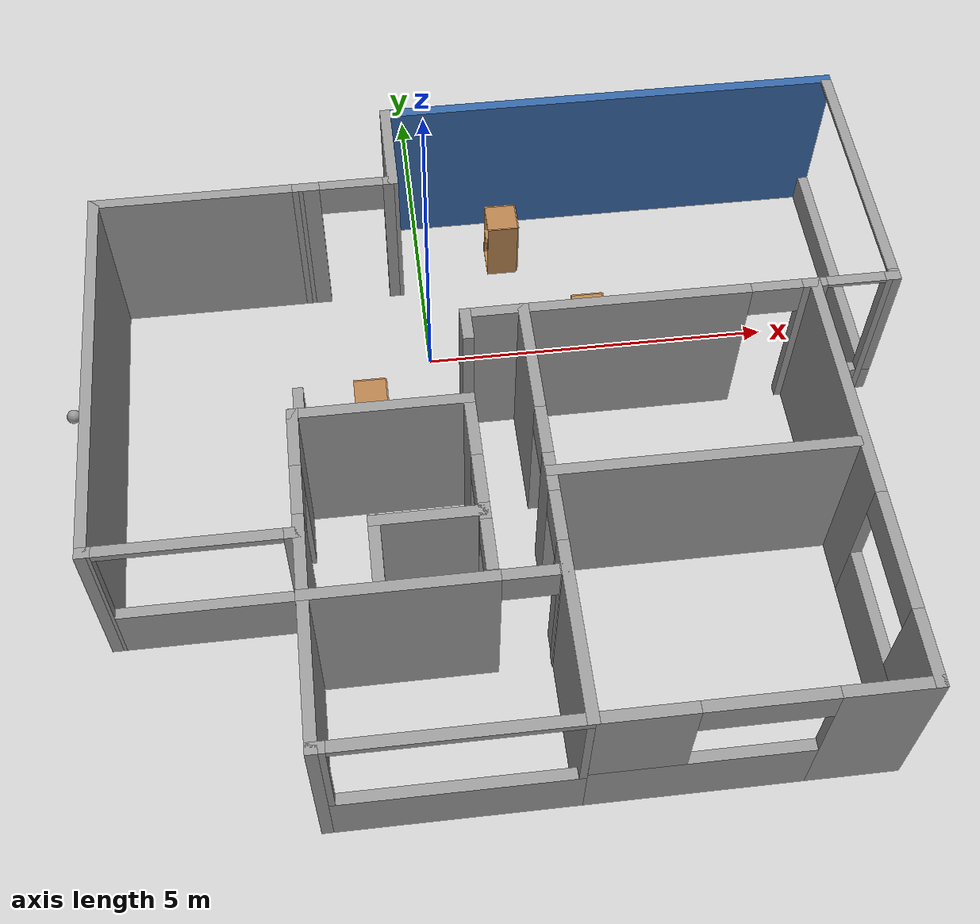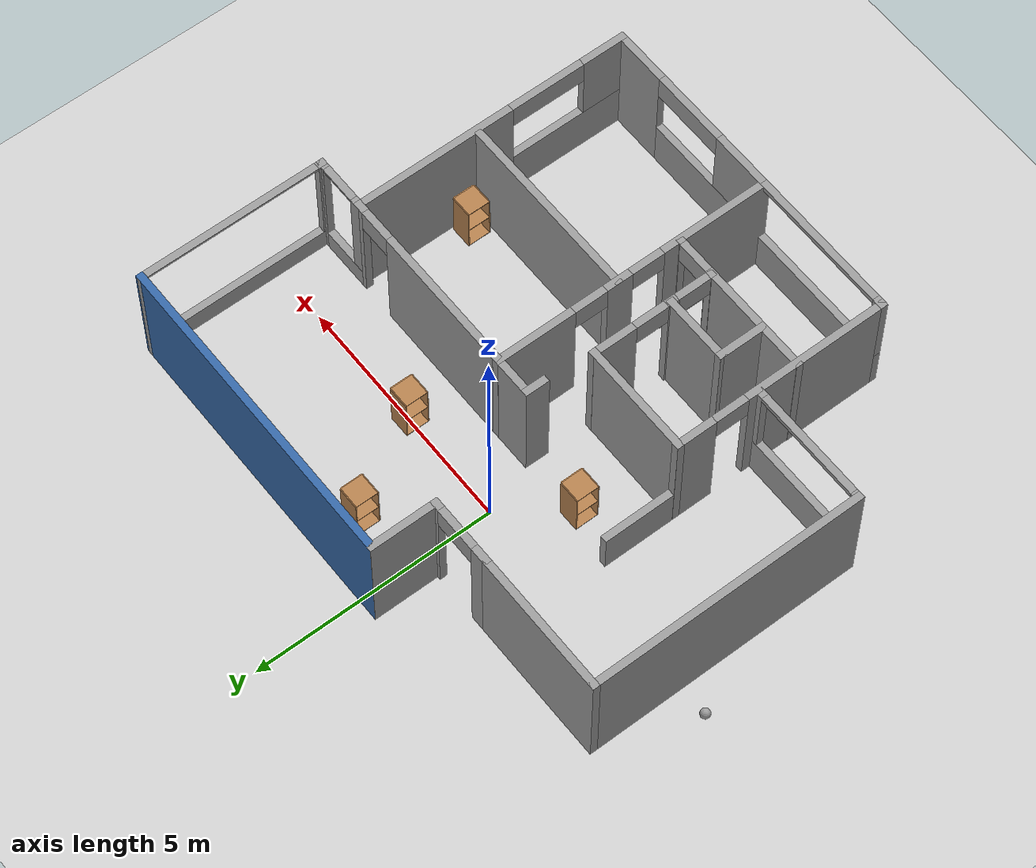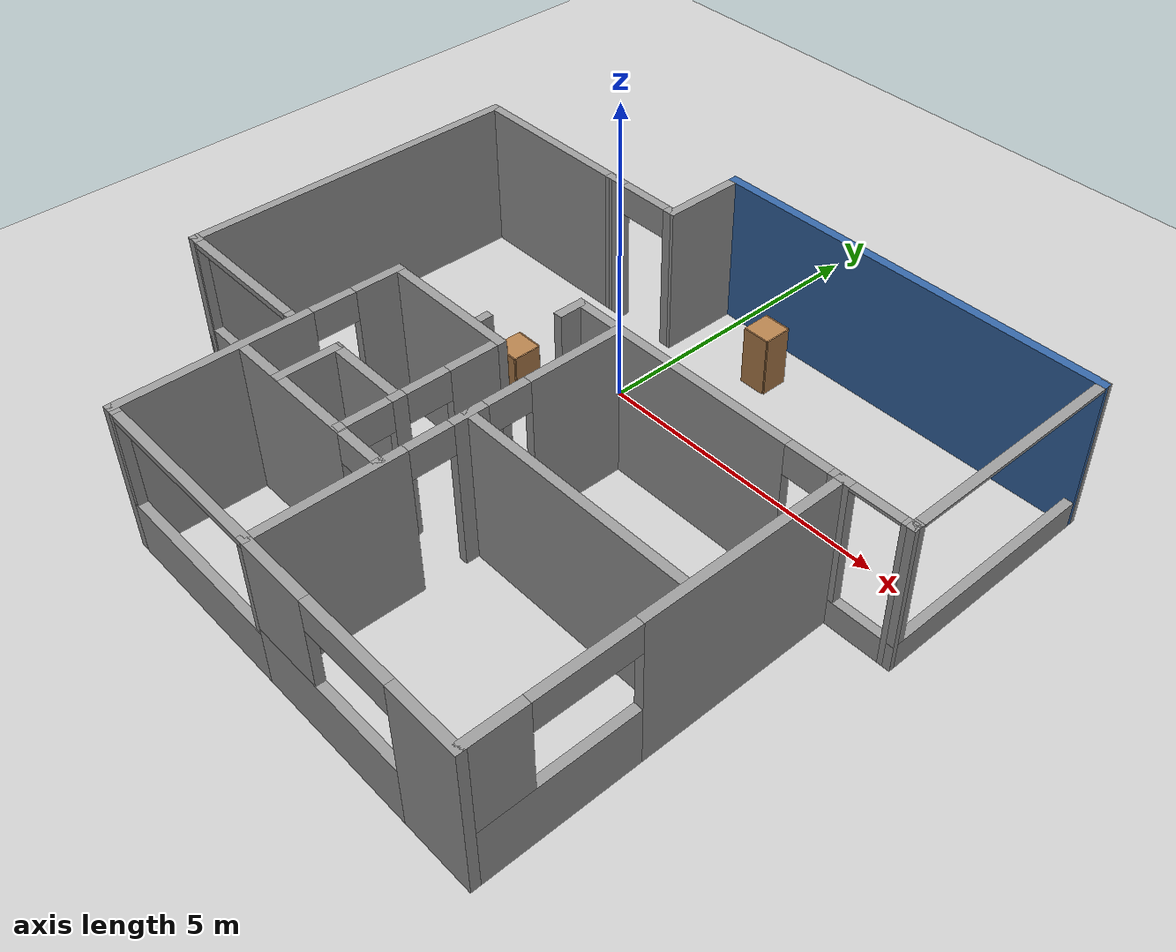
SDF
<sdf version="1.7">
 <world name="default">
  <plugin name="hello" filename="../build/libhello.so"/>
  <model name="ground_plane">
   <static>1</static>
   <link name="link">
    <collision name="collision">
     <geometry><plane><normal>0 0 1</normal><size>100 100</size></plane></geometry>
     <surface>
      <contact><collide_bitmask>65535</collide_bitmask></contact>
      <friction><ode><mu>100</mu><mu2>50</mu2></ode></friction>
     </surface>
    </collision>
    <visual name="visual">
     <cast_shadows>0</cast_shadows>
     <geometry><plane><normal>0 0 1</normal><size>100 100</size></plane></geometry>
     <material>
      <script><uri>file://media/materials/scripts/gazebo.material</uri><name>Gazebo/Grey</name></script>
     </material>
    </visual>
   </link>
  </model>
  <gravity>0 0 -9.8</gravity>
  <magnetic_field>6e-06 2.3e-05 -4.2e-05</magnetic_field>
  <atmosphere type="adiabatic"/>
  <physics type="ode">
   <max_step_size>0.001</max_step_size>
   <real_time_factor>1</real_time_factor>
   <real_time_update_rate>1000</real_time_update_rate>
  </physics>
  <scene><ambient>0.4 0.4 0.4 1</ambient><background>0.7 0.7 0.7 1</background><shadows>1</shadows></scene>
  <spherical_coordinates>
   <surface_model>EARTH_WGS84</surface_model>
   <latitude_deg>0</latitude_deg>
   <longitude_deg>0</longitude_deg>
   <elevation>0</elevation>
   <heading_deg>0</heading_deg>
  </spherical_coordinates>
  <model name="Myhouse">
   <link name="Wall_0">
    <pose>2.10158 4.8407 0 0 -0 0</pose>
    <visual name="Wall_0_Visual">
     <pose>0 0 1.25 0 -0 0</pose>
     <geometry><box><size>6.75 0.15 2.5</size></box></geometry>
     <material>
      <script><uri>file://media/materials/scripts/gazebo.material</uri><name>Gazebo/Grey</name></script>
      <ambient>0.203922 0.396078 0.643137 1</ambient>
      <shader type="pixel"/>
     </material>
     <meta><layer>0</layer></meta>
    </visual>
    <collision name="Wall_0_Collision">
     <pose>0 0 1.25 0 -0 0</pose>
     <geometry><box><size>6.75 0.15 2.5</size></box></geometry>
     <surface>
      <friction>
       <ode><mu>1</mu><mu2>1</mu2><fdir1>0 0 0</fdir1><slip1>0</slip1><slip2>0</slip2></ode>
       <torsional>
        <coefficient>1</coefficient>
        <patch_radius>0</patch_radius>
        <surface_radius>0</surface_radius>
        <use_patch_radius>1</use_patch_radius>
        <ode><slip>0</slip></ode>
       </torsional>
      </friction>
      <bounce><restitution_coefficient>0</restitution_coefficient><threshold>1e+06</threshold></bounce>
      <contact>
       <collide_without_contact>0</collide_without_contact>
       <collide_without_contact_bitmask>1</collide_without_contact_bitmask>
       <collide_bitmask>1</collide_bitmask>
       <ode>
        <soft_cfm>0</soft_cfm>
        <soft_erp>0.2</soft_erp>
        <kp>1e+13</kp>
        <kd>1</kd>
        <max_vel>0.01</max_vel>
        <min_depth>0</min_depth>
       </ode>
       <bullet>
        <split_impulse>1</split_impulse>
        <split_impulse_penetration_threshold>-0.01</split_impulse_penetration_threshold>
        <soft_cfm>0</soft_cfm>
        <soft_erp>0.2</soft_erp>
        <kp>1e+13</kp>
        <kd>1</kd>
       </bullet>
      </contact>
     </surface>
    </collision>
   </link>
   <link name="Wall_1">
    <pose>5.39997 2.92495 0 0 0 -1.57164</pose>
    <visual name="Wall_1_Visual_0">
     <pose>-1.94391 0 1.25 0 -0 0</pose>
     <geometry><box><size>0.093734 0.15 2.5</size></box></geometry>
     <material>
      <script><uri>file://media/materials/scripts/gazebo.material</uri><name>Gazebo/Grey</name></script>
      <ambient>1 1 1 1</ambient>
      <shader type="pixel"/>
     </material>
     <meta><layer>0</layer></meta>
    </visual>
    <visual name="Wall_1_Visual_1">
     <pose>0.046867 0 0.225 0 -0 0</pose>
     <geometry><box><size>3.88783 0.15 0.45</size></box></geometry>
     <material>
      <script><uri>file://media/materials/scripts/gazebo.material</uri><name>Gazebo/Grey</name></script>
      <ambient>1 1 1 1</ambient>
      <shader type="pixel"/>
     </material>
     <meta><layer>0</layer></meta>
    </visual>
    <visual name="Wall_1_Visual_2">
     <pose>1.89687 0 1.475 0 -0 0</pose>
     <geometry><box><size>0.187826 0.15 2.05</size></box></geometry>
     <material>
      <script><uri>file://media/materials/scripts/gazebo.material</uri><name>Gazebo/Grey</name></script>
      <ambient>1 1 1 1</ambient>
      <shader type="pixel"/>
     </material>
     <meta><layer>0</layer></meta>
    </visual>
    <visual name="Wall_1_Visual_3">
     <pose>-0.047046 0 2.475 0 -0 0</pose>
     <geometry><box><size>3.7 0.15 0.05</size></box></geometry>
     <material>
      <script><uri>file://media/materials/scripts/gazebo.material</uri><name>Gazebo/Grey</name></script>
      <ambient>1 1 1 1</ambient>
      <shader type="pixel"/>
     </material>
     <meta><layer>0</layer></meta>
    </visual>
    <collision name="Wall_1_Collision_0">
     <pose>-1.94391 0 1.25 0 -0 0</pose>
     <geometry><box><size>0.093734 0.15 2.5</size></box></geometry>
     <surface>
      <friction>
       <ode><mu>1</mu><mu2>1</mu2><fdir1>0 0 0</fdir1><slip1>0</slip1><slip2>0</slip2></ode>
       <torsional>
        <coefficient>1</coefficient>
        <patch_radius>0</patch_radius>
        <surface_radius>0</surface_radius>
        <use_patch_radius>1</use_patch_radius>
        <ode><slip>0</slip></ode>
       </torsional>
      </friction>
      <bounce><restitution_coefficient>0</restitution_coefficient><threshold>1e+06</threshold></bounce>
      <contact>
       <collide_without_contact>0</collide_without_contact>
       <collide_without_contact_bitmask>1</collide_without_contact_bitmask>
       <collide_bitmask>1</collide_bitmask>
       <ode>
        <soft_cfm>0</soft_cfm>
        <soft_erp>0.2</soft_erp>
        <kp>1e+13</kp>
        <kd>1</kd>
        <max_vel>0.01</max_vel>
        <min_depth>0</min_depth>
       </ode>
       <bullet>
        <split_impulse>1</split_impulse>
        <split_impulse_penetration_threshold>-0.01</split_impulse_penetration_threshold>
        <soft_cfm>0</soft_cfm>
        <soft_erp>0.2</soft_erp>
        <kp>1e+13</kp>
        <kd>1</kd>
       </bullet>
      </contact>
     </surface>
    </collision>
    <collision name="Wall_1_Collision_1">
     <pose>0.046867 0 0.225 0 -0 0</pose>
     <geometry><box><size>3.88783 0.15 0.45</size></box></geometry>
     <surface>
      <friction>
       <ode><mu>1</mu><mu2>1</mu2><fdir1>0 0 0</fdir1><slip1>0</slip1><slip2>0</slip2></ode>
       <torsional>
        <coefficient>1</coefficient>
        <patch_radius>0</patch_radius>
        <surface_radius>0</surface_radius>
        <use_patch_radius>1</use_patch_radius>
        <ode><slip>0</slip></ode>
       </torsional>
      </friction>
      <bounce><restitution_coefficient>0</restitution_coefficient><threshold>1e+06</threshold></bounce>
      <contact>
       <collide_without_contact>0</collide_without_contact>
       <collide_without_contact_bitmask>1</collide_without_contact_bitmask>
       <collide_bitmask>1</collide_bitmask>
       <ode>
        <soft_cfm>0</soft_cfm>
        <soft_erp>0.2</soft_erp>
        <kp>1e+13</kp>
        <kd>1</kd>
        <max_vel>0.01</max_vel>
        <min_depth>0</min_depth>
       </ode>
       <bullet>
        <split_impulse>1</split_impulse>
        <split_impulse_penetration_threshold>-0.01</split_impulse_penetration_threshold>
        <soft_cfm>0</soft_cfm>
        <soft_erp>0.2</soft_erp>
        <kp>1e+13</kp>
        <kd>1</kd>
       </bullet>
      </contact>
     </surface>
    </collision>
    <collision name="Wall_1_Collision_2">
     <pose>1.89687 0 1.475 0 -0 0</pose>
     <geometry><box><size>0.187826 0.15 2.05</size></box></geometry>
     <surface>
      <friction>
       <ode><mu>1</mu><mu2>1</mu2><fdir1>0 0 0</fdir1><slip1>0</slip1><slip2>0</slip2></ode>
       <torsional>
        <coefficient>1</coefficient>
        <patch_radius>0</patch_radius>
        <surface_radius>0</surface_radius>
        <use_patch_radius>1</use_patch_radius>
        <ode><slip>0</slip></ode>
       </torsional>
      </friction>
      <bounce><restitution_coefficient>0</restitution_coefficient><threshold>1e+06</threshold></bounce>
      <contact>
       <collide_without_contact>0</collide_without_contact>
       <collide_without_contact_bitmask>1</collide_without_contact_bitmask>
       <collide_bitmask>1</collide_bitmask>
       <ode>
        <soft_cfm>0</soft_cfm>
        <soft_erp>0.2</soft_erp>
        <kp>1e+13</kp>
        <kd>1</kd>
        <max_vel>0.01</max_vel>
        <min_depth>0</min_depth>
       </ode>
       <bullet>
        <split_impulse>1</split_impulse>
        <split_impulse_penetration_threshold>-0.01</split_impulse_penetration_threshold>
        <soft_cfm>0</soft_cfm>
        <soft_erp>0.2</soft_erp>
        <kp>1e+13</kp>
        <kd>1</kd>
       </bullet>
      </contact>
     </surface>
    </collision>
    <collision name="Wall_1_Collision_3">
     <pose>-0.047046 0 2.475 0 -0 0</pose>
     <geometry><box><size>3.7 0.15 0.05</size></box></geometry>
     <surface>
      <friction>
       <ode><mu>1</mu><mu2>1</mu2><fdir1>0 0 0</fdir1><slip1>0</slip1><slip2>0</slip2></ode>
       <torsional>
        <coefficient>1</coefficient>
        <patch_radius>0</patch_radius>
        <surface_radius>0</surface_radius>
        <use_patch_radius>1</use_patch_radius>
        <ode><slip>0</slip></ode>
       </torsional>
      </friction>
      <bounce><restitution_coefficient>0</restitution_coefficient><threshold>1e+06</threshold></bounce>
      <contact>
       <collide_without_contact>0</collide_without_contact>
       <collide_without_contact_bitmask>1</collide_without_contact_bitmask>
       <collide_bitmask>1</collide_bitmask>
       <ode>
        <soft_cfm>0</soft_cfm>
        <soft_erp>0.2</soft_erp>
        <kp>1e+13</kp>
        <kd>1</kd>
        <max_vel>0.01</max_vel>
        <min_depth>0</min_depth>
       </ode>
       <bullet>
        <split_impulse>1</split_impulse>
        <split_impulse_penetration_threshold>-0.01</split_impulse_penetration_threshold>
        <soft_cfm>0</soft_cfm>
        <soft_erp>0.2</soft_erp>
        <kp>1e+13</kp>
        <kd>1</kd>
       </bullet>
      </contact>
     </surface>
    </collision>
   </link>
   <link name="Wall_13">
    <pose>1.92675 1.00921 0 0 -0 3.14159</pose>
    <visual name="Wall_13_Visual_0">
     <pose>-2.32196 0 1.25 0 -0 0</pose>
     <geometry><box><size>0.249291 0.15 2.5</size></box></geometry>
     <material>
      <script><uri>file://media/materials/scripts/gazebo.material</uri><name>Gazebo/Grey</name></script>
      <ambient>1 1 1 1</ambient>
      <shader type="pixel"/>
     </material>
     <meta><layer>0</layer></meta>
    </visual>
    <visual name="Wall_13_Visual_1">
     <pose>0.474646 0 1.25 0 -0 0</pose>
     <geometry><box><size>3.94392 0.15 2.5</size></box></geometry>
     <material>
      <script><uri>file://media/materials/scripts/gazebo.material</uri><name>Gazebo/Grey</name></script>
      <ambient>1 1 1 1</ambient>
      <shader type="pixel"/>
     </material>
     <meta><layer>0</layer></meta>
    </visual>
    <visual name="Wall_13_Visual_2">
     <pose>-1.84732 0 2.25 0 -0 0</pose>
     <geometry><box><size>0.7 0.15 0.5</size></box></geometry>
     <material>
      <script><uri>file://media/materials/scripts/gazebo.material</uri><name>Gazebo/Grey</name></script>
      <ambient>1 1 1 1</ambient>
      <shader type="pixel"/>
     </material>
     <meta><layer>0</layer></meta>
    </visual>
    <collision name="Wall_13_Collision_0">
     <pose>-2.32196 0 1.25 0 -0 0</pose>
     <geometry><box><size>0.249291 0.15 2.5</size></box></geometry>
     <surface>
      <friction>
       <ode><mu>1</mu><mu2>1</mu2><fdir1>0 0 0</fdir1><slip1>0</slip1><slip2>0</slip2></ode>
       <torsional>
        <coefficient>1</coefficient>
        <patch_radius>0</patch_radius>
        <surface_radius>0</surface_radius>
        <use_patch_radius>1</use_patch_radius>
        <ode><slip>0</slip></ode>
       </torsional>
      </friction>
      <bounce><restitution_coefficient>0</restitution_coefficient><threshold>1e+06</threshold></bounce>
      <contact>
       <collide_without_contact>0</collide_without_contact>
       <collide_without_contact_bitmask>1</collide_without_contact_bitmask>
       <collide_bitmask>1</collide_bitmask>
       <ode>
        <soft_cfm>0</soft_cfm>
        <soft_erp>0.2</soft_erp>
        <kp>1e+13</kp>
        <kd>1</kd>
        <max_vel>0.01</max_vel>
        <min_depth>0</min_depth>
       </ode>
       <bullet>
        <split_impulse>1</split_impulse>
        <split_impulse_penetration_threshold>-0.01</split_impulse_penetration_threshold>
        <soft_cfm>0</soft_cfm>
        <soft_erp>0.2</soft_erp>
        <kp>1e+13</kp>
        <kd>1</kd>
       </bullet>
      </contact>
     </surface>
    </collision>
    <collision name="Wall_13_Collision_1">
     <pose>0.474646 0 1.25 0 -0 0</pose>
     <geometry><box><size>3.94392 0.15 2.5</size></box></geometry>
     <surface>
      <friction>
       <ode><mu>1</mu><mu2>1</mu2><fdir1>0 0 0</fdir1><slip1>0</slip1><slip2>0</slip2></ode>
       <torsional>
        <coefficient>1</coefficient>
        <patch_radius>0</patch_radius>
        <surface_radius>0</surface_radius>
        <use_patch_radius>1</use_patch_radius>
        <ode><slip>0</slip></ode>
       </torsional>
      </friction>
      <bounce><restitution_coefficient>0</restitution_coefficient><threshold>1e+06</threshold></bounce>
      <contact>
       <collide_without_contact>0</collide_without_contact>
       <collide_without_contact_bitmask>1</collide_without_contact_bitmask>
       <collide_bitmask>1</collide_bitmask>
       <ode>
        <soft_cfm>0</soft_cfm>
        <soft_erp>0.2</soft_erp>
        <kp>1e+13</kp>
        <kd>1</kd>
        <max_vel>0.01</max_vel>
        <min_depth>0</min_depth>
       </ode>
       <bullet>
        <split_impulse>1</split_impulse>
        <split_impulse_penetration_threshold>-0.01</split_impulse_penetration_threshold>
        <soft_cfm>0</soft_cfm>
        <soft_erp>0.2</soft_erp>
        <kp>1e+13</kp>
        <kd>1</kd>
       </bullet>
      </contact>
     </surface>
    </collision>
    <collision name="Wall_13_Collision_2">
     <pose>-1.84732 0 2.25 0 -0 0</pose>
     <geometry><box><size>0.7 0.15 0.5</size></box></geometry>
     <surface>
      <friction>
       <ode><mu>1</mu><mu2>1</mu2><fdir1>0 0 0</fdir1><slip1>0</slip1><slip2>0</slip2></ode>
       <torsional>
        <coefficient>1</coefficient>
        <patch_radius>0</patch_radius>
        <surface_radius>0</surface_radius>
        <use_patch_radius>1</use_patch_radius>
        <ode><slip>0</slip></ode>
       </torsional>
      </friction>
      <bounce><restitution_coefficient>0</restitution_coefficient><threshold>1e+06</threshold></bounce>
      <contact>
       <collide_without_contact>0</collide_without_contact>
       <collide_without_contact_bitmask>1</collide_without_contact_bitmask>
       <collide_bitmask>1</collide_bitmask>
       <ode>
        <soft_cfm>0</soft_cfm>
        <soft_erp>0.2</soft_erp>
        <kp>1e+13</kp>
        <kd>1</kd>
        <max_vel>0.01</max_vel>
        <min_depth>0</min_depth>
       </ode>
       <bullet>
        <split_impulse>1</split_impulse>
        <split_impulse_penetration_threshold>-0.01</split_impulse_penetration_threshold>
        <soft_cfm>0</soft_cfm>
        <soft_erp>0.2</soft_erp>
        <kp>1e+13</kp>
        <kd>1</kd>
       </bullet>
      </contact>
     </surface>
    </collision>
   </link>
   <link name="Wall_17">
    <pose>2.26458 -1.5613 0 0 -0 3.14159</pose>
    <visual name="Wall_17_Visual">
     <pose>0 0 1.25 0 -0 0</pose>
     <geometry><box><size>4 0.15 2.5</size></box></geometry>
     <material>
      <script><uri>file://media/materials/scripts/gazebo.material</uri><name>Gazebo/Grey</name></script>
      <ambient>1 1 1 1</ambient>
      <shader type="pixel"/>
     </material>
     <meta><layer>0</layer></meta>
    </visual>
    <collision name="Wall_17_Collision">
     <pose>0 0 1.25 0 -0 0</pose>
     <geometry><box><size>4 0.15 2.5</size></box></geometry>
     <surface>
      <friction>
       <ode><mu>1</mu><mu2>1</mu2><fdir1>0 0 0</fdir1><slip1>0</slip1><slip2>0</slip2></ode>
       <torsional>
        <coefficient>1</coefficient>
        <patch_radius>0</patch_radius>
        <surface_radius>0</surface_radius>
        <use_patch_radius>1</use_patch_radius>
        <ode><slip>0</slip></ode>
       </torsional>
      </friction>
      <bounce><restitution_coefficient>0</restitution_coefficient><threshold>1e+06</threshold></bounce>
      <contact>
       <collide_without_contact>0</collide_without_contact>
       <collide_without_contact_bitmask>1</collide_without_contact_bitmask>
       <collide_bitmask>1</collide_bitmask>
       <ode>
        <soft_cfm>0</soft_cfm>
        <soft_erp>0.2</soft_erp>
        <kp>1e+13</kp>
        <kd>1</kd>
        <max_vel>0.01</max_vel>
        <min_depth>0</min_depth>
       </ode>
       <bullet>
        <split_impulse>1</split_impulse>
        <split_impulse_penetration_threshold>-0.01</split_impulse_penetration_threshold>
        <soft_cfm>0</soft_cfm>
        <soft_erp>0.2</soft_erp>
        <kp>1e+13</kp>
        <kd>1</kd>
       </bullet>
      </contact>
     </surface>
    </collision>
   </link>
   <link name="Wall_23">
    <pose>0.334124 -1.9144 0 0 -0 1.5708</pose>
    <visual name="Wall_23_Visual_0">
     <pose>-1.81879 0 1.25 0 -0 0</pose>
     <geometry><box><size>2.36243 0.15 2.5</size></box></geometry>
     <material>
      <script><uri>file://media/materials/scripts/gazebo.material</uri><name>Gazebo/Grey</name></script>
      <ambient>1 1 1 1</ambient>
      <shader type="pixel"/>
     </material>
     <meta><layer>0</layer></meta>
    </visual>
    <visual name="Wall_23_Visual_1">
     <pose>0.340045 0 1.25 0 -0 0</pose>
     <geometry><box><size>0.555232 0.15 2.5</size></box></geometry>
     <material>
      <script><uri>file://media/materials/scripts/gazebo.material</uri><name>Gazebo/Grey</name></script>
      <ambient>1 1 1 1</ambient>
      <shader type="pixel"/>
     </material>
     <meta><layer>0</layer></meta>
    </visual>
    <visual name="Wall_23_Visual_2">
     <pose>2.15883 0 1.25 0 -0 0</pose>
     <geometry><box><size>1.68234 0.15 2.5</size></box></geometry>
     <material>
      <script><uri>file://media/materials/scripts/gazebo.material</uri><name>Gazebo/Grey</name></script>
      <ambient>1 1 1 1</ambient>
      <shader type="pixel"/>
     </material>
     <meta><layer>0</layer></meta>
    </visual>
    <visual name="Wall_23_Visual_3">
     <pose>-0.287571 0 2.25 0 -0 0</pose>
     <geometry><box><size>0.7 0.15 0.5</size></box></geometry>
     <material>
      <script><uri>file://media/materials/scripts/gazebo.material</uri><name>Gazebo/Grey</name></script>
      <ambient>1 1 1 1</ambient>
      <shader type="pixel"/>
     </material>
     <meta><layer>0</layer></meta>
    </visual>
    <visual name="Wall_23_Visual_4">
     <pose>0.967661 0 2.25 0 -0 0</pose>
     <geometry><box><size>0.7 0.15 0.5</size></box></geometry>
     <material>
      <script><uri>file://media/materials/scripts/gazebo.material</uri><name>Gazebo/Grey</name></script>
      <ambient>1 1 1 1</ambient>
      <shader type="pixel"/>
     </material>
     <meta><layer>0</layer></meta>
    </visual>
    <collision name="Wall_23_Collision_0">
     <pose>-1.81879 0 1.25 0 -0 0</pose>
     <geometry><box><size>2.36243 0.15 2.5</size></box></geometry>
     <surface>
      <friction>
       <ode><mu>1</mu><mu2>1</mu2><fdir1>0 0 0</fdir1><slip1>0</slip1><slip2>0</slip2></ode>
       <torsional>
        <coefficient>1</coefficient>
        <patch_radius>0</patch_radius>
        <surface_radius>0</surface_radius>
        <use_patch_radius>1</use_patch_radius>
        <ode><slip>0</slip></ode>
       </torsional>
      </friction>
      <bounce><restitution_coefficient>0</restitution_coefficient><threshold>1e+06</threshold></bounce>
      <contact>
       <collide_without_contact>0</collide_without_contact>
       <collide_without_contact_bitmask>1</collide_without_contact_bitmask>
       <collide_bitmask>1</collide_bitmask>
       <ode>
        <soft_cfm>0</soft_cfm>
        <soft_erp>0.2</soft_erp>
        <kp>1e+13</kp>
        <kd>1</kd>
        <max_vel>0.01</max_vel>
        <min_depth>0</min_depth>
       </ode>
       <bullet>
        <split_impulse>1</split_impulse>
        <split_impulse_penetration_threshold>-0.01</split_impulse_penetration_threshold>
        <soft_cfm>0</soft_cfm>
        <soft_erp>0.2</soft_erp>
        <kp>1e+13</kp>
        <kd>1</kd>
       </bullet>
      </contact>
     </surface>
    </collision>
    <collision name="Wall_23_Collision_1">
     <pose>0.340045 0 1.25 0 -0 0</pose>
     <geometry><box><size>0.555232 0.15 2.5</size></box></geometry>
     <surface>
      <friction>
       <ode><mu>1</mu><mu2>1</mu2><fdir1>0 0 0</fdir1><slip1>0</slip1><slip2>0</slip2></ode>
       <torsional>
        <coefficient>1</coefficient>
        <patch_radius>0</patch_radius>
        <surface_radius>0</surface_radius>
        <use_patch_radius>1</use_patch_radius>
        <ode><slip>0</slip></ode>
       </torsional>
      </friction>
      <bounce><restitution_coefficient>0</restitution_coefficient><threshold>1e+06</threshold></bounce>
      <contact>
       <collide_without_contact>0</collide_without_contact>
       <collide_without_contact_bitmask>1</collide_without_contact_bitmask>
       <collide_bitmask>1</collide_bitmask>
       <ode>
        <soft_cfm>0</soft_cfm>
        <soft_erp>0.2</soft_erp>
        <kp>1e+13</kp>
        <kd>1</kd>
        <max_vel>0.01</max_vel>
        <min_depth>0</min_depth>
       </ode>
       <bullet>
        <split_impulse>1</split_impulse>
        <split_impulse_penetration_threshold>-0.01</split_impulse_penetration_threshold>
        <soft_cfm>0</soft_cfm>
        <soft_erp>0.2</soft_erp>
        <kp>1e+13</kp>
        <kd>1</kd>
       </bullet>
      </contact>
     </surface>
    </collision>
    <collision name="Wall_23_Collision_2">
     <pose>2.15883 0 1.25 0 -0 0</pose>
     <geometry><box><size>1.68234 0.15 2.5</size></box></geometry>
     <surface>
      <friction>
       <ode><mu>1</mu><mu2>1</mu2><fdir1>0 0 0</fdir1><slip1>0</slip1><slip2>0</slip2></ode>
       <torsional>
        <coefficient>1</coefficient>
        <patch_radius>0</patch_radius>
        <surface_radius>0</surface_radius>
        <use_patch_radius>1</use_patch_radius>
        <ode><slip>0</slip></ode>
       </torsional>
      </friction>
      <bounce><restitution_coefficient>0</restitution_coefficient><threshold>1e+06</threshold></bounce>
      <contact>
       <collide_without_contact>0</collide_without_contact>
       <collide_without_contact_bitmask>1</collide_without_contact_bitmask>
       <collide_bitmask>1</collide_bitmask>
       <ode>
        <soft_cfm>0</soft_cfm>
        <soft_erp>0.2</soft_erp>
        <kp>1e+13</kp>
        <kd>1</kd>
        <max_vel>0.01</max_vel>
        <min_depth>0</min_depth>
       </ode>
       <bullet>
        <split_impulse>1</split_impulse>
        <split_impulse_penetration_threshold>-0.01</split_impulse_penetration_threshold>
        <soft_cfm>0</soft_cfm>
        <soft_erp>0.2</soft_erp>
        <kp>1e+13</kp>
        <kd>1</kd>
       </bullet>
      </contact>
     </surface>
    </collision>
    <collision name="Wall_23_Collision_3">
     <pose>-0.287571 0 2.25 0 -0 0</pose>
     <geometry><box><size>0.7 0.15 0.5</size></box></geometry>
     <surface>
      <friction>
       <ode><mu>1</mu><mu2>1</mu2><fdir1>0 0 0</fdir1><slip1>0</slip1><slip2>0</slip2></ode>
       <torsional>
        <coefficient>1</coefficient>
        <patch_radius>0</patch_radius>
        <surface_radius>0</surface_radius>
        <use_patch_radius>1</use_patch_radius>
        <ode><slip>0</slip></ode>
       </torsional>
      </friction>
      <bounce><restitution_coefficient>0</restitution_coefficient><threshold>1e+06</threshold></bounce>
      <contact>
       <collide_without_contact>0</collide_without_contact>
       <collide_without_contact_bitmask>1</collide_without_contact_bitmask>
       <collide_bitmask>1</collide_bitmask>
       <ode>
        <soft_cfm>0</soft_cfm>
        <soft_erp>0.2</soft_erp>
        <kp>1e+13</kp>
        <kd>1</kd>
        <max_vel>0.01</max_vel>
        <min_depth>0</min_depth>
       </ode>
       <bullet>
        <split_impulse>1</split_impulse>
        <split_impulse_penetration_threshold>-0.01</split_impulse_penetration_threshold>
        <soft_cfm>0</soft_cfm>
        <soft_erp>0.2</soft_erp>
        <kp>1e+13</kp>
        <kd>1</kd>
       </bullet>
      </contact>
     </surface>
    </collision>
    <collision name="Wall_23_Collision_4">
     <pose>0.967661 0 2.25 0 -0 0</pose>
     <geometry><box><size>0.7 0.15 0.5</size></box></geometry>
     <surface>
      <friction>
       <ode><mu>1</mu><mu2>1</mu2><fdir1>0 0 0</fdir1><slip1>0</slip1><slip2>0</slip2></ode>
       <torsional>
        <coefficient>1</coefficient>
        <patch_radius>0</patch_radius>
        <surface_radius>0</surface_radius>
        <use_patch_radius>1</use_patch_radius>
        <ode><slip>0</slip></ode>
       </torsional>
      </friction>
      <bounce><restitution_coefficient>0</restitution_coefficient><threshold>1e+06</threshold></bounce>
      <contact>
       <collide_without_contact>0</collide_without_contact>
       <collide_without_contact_bitmask>1</collide_without_contact_bitmask>
       <collide_bitmask>1</collide_bitmask>
       <ode>
        <soft_cfm>0</soft_cfm>
        <soft_erp>0.2</soft_erp>
        <kp>1e+13</kp>
        <kd>1</kd>
        <max_vel>0.01</max_vel>
        <min_depth>0</min_depth>
       </ode>
       <bullet>
        <split_impulse>1</split_impulse>
        <split_impulse_penetration_threshold>-0.01</split_impulse_penetration_threshold>
        <soft_cfm>0</soft_cfm>
        <soft_erp>0.2</soft_erp>
        <kp>1e+13</kp>
        <kd>1</kd>
       </bullet>
      </contact>
     </surface>
    </collision>
   </link>
   <link name="Wall_27">
    <pose>-1.25954 -2.94166 0 0 -0 0</pose>
    <visual name="Wall_27_Visual_0">
     <pose>-0.409905 0 1.25 0 -0 0</pose>
     <geometry><box><size>2.43019 0.15 2.5</size></box></geometry>
     <material>
      <script><uri>file://media/materials/scripts/gazebo.material</uri><name>Gazebo/Grey</name></script>
      <ambient>1 1 1 1</ambient>
      <shader type="pixel"/>
     </material>
     <meta><layer>0</layer></meta>
    </visual>
    <visual name="Wall_27_Visual_1">
     <pose>1.56509 0 1.25 0 -0 0</pose>
     <geometry><box><size>0.119811 0.15 2.5</size></box></geometry>
     <material>
      <script><uri>file://media/materials/scripts/gazebo.material</uri><name>Gazebo/Grey</name></script>
      <ambient>1 1 1 1</ambient>
      <shader type="pixel"/>
     </material>
     <meta><layer>0</layer></meta>
    </visual>
    <visual name="Wall_27_Visual_2">
     <pose>1.15519 0 2.25 0 -0 0</pose>
     <geometry><box><size>0.7 0.15 0.5</size></box></geometry>
     <material>
      <script><uri>file://media/materials/scripts/gazebo.material</uri><name>Gazebo/Grey</name></script>
      <ambient>1 1 1 1</ambient>
      <shader type="pixel"/>
     </material>
     <meta><layer>0</layer></meta>
    </visual>
    <collision name="Wall_27_Collision_0">
     <pose>-0.409905 0 1.25 0 -0 0</pose>
     <geometry><box><size>2.43019 0.15 2.5</size></box></geometry>
     <surface>
      <friction>
       <ode><mu>1</mu><mu2>1</mu2><fdir1>0 0 0</fdir1><slip1>0</slip1><slip2>0</slip2></ode>
       <torsional>
        <coefficient>1</coefficient>
        <patch_radius>0</patch_radius>
        <surface_radius>0</surface_radius>
        <use_patch_radius>1</use_patch_radius>
        <ode><slip>0</slip></ode>
       </torsional>
      </friction>
      <bounce><restitution_coefficient>0</restitution_coefficient><threshold>1e+06</threshold></bounce>
      <contact>
       <collide_without_contact>0</collide_without_contact>
       <collide_without_contact_bitmask>1</collide_without_contact_bitmask>
       <collide_bitmask>1</collide_bitmask>
       <ode>
        <soft_cfm>0</soft_cfm>
        <soft_erp>0.2</soft_erp>
        <kp>1e+13</kp>
        <kd>1</kd>
        <max_vel>0.01</max_vel>
        <min_depth>0</min_depth>
       </ode>
       <bullet>
        <split_impulse>1</split_impulse>
        <split_impulse_penetration_threshold>-0.01</split_impulse_penetration_threshold>
        <soft_cfm>0</soft_cfm>
        <soft_erp>0.2</soft_erp>
        <kp>1e+13</kp>
        <kd>1</kd>
       </bullet>
      </contact>
     </surface>
    </collision>
    <collision name="Wall_27_Collision_1">
     <pose>1.56509 0 1.25 0 -0 0</pose>
     <geometry><box><size>0.119811 0.15 2.5</size></box></geometry>
     <surface>
      <friction>
       <ode><mu>1</mu><mu2>1</mu2><fdir1>0 0 0</fdir1><slip1>0</slip1><slip2>0</slip2></ode>
       <torsional>
        <coefficient>1</coefficient>
        <patch_radius>0</patch_radius>
        <surface_radius>0</surface_radius>
        <use_patch_radius>1</use_patch_radius>
        <ode><slip>0</slip></ode>
       </torsional>
      </friction>
      <bounce><restitution_coefficient>0</restitution_coefficient><threshold>1e+06</threshold></bounce>
      <contact>
       <collide_without_contact>0</collide_without_contact>
       <collide_without_contact_bitmask>1</collide_without_contact_bitmask>
       <collide_bitmask>1</collide_bitmask>
       <ode>
        <soft_cfm>0</soft_cfm>
        <soft_erp>0.2</soft_erp>
        <kp>1e+13</kp>
        <kd>1</kd>
        <max_vel>0.01</max_vel>
        <min_depth>0</min_depth>
       </ode>
       <bullet>
        <split_impulse>1</split_impulse>
        <split_impulse_penetration_threshold>-0.01</split_impulse_penetration_threshold>
        <soft_cfm>0</soft_cfm>
        <soft_erp>0.2</soft_erp>
        <kp>1e+13</kp>
        <kd>1</kd>
       </bullet>
      </contact>
     </surface>
    </collision>
    <collision name="Wall_27_Collision_2">
     <pose>1.15519 0 2.25 0 -0 0</pose>
     <geometry><box><size>0.7 0.15 0.5</size></box></geometry>
     <surface>
      <friction>
       <ode><mu>1</mu><mu2>1</mu2><fdir1>0 0 0</fdir1><slip1>0</slip1><slip2>0</slip2></ode>
       <torsional>
        <coefficient>1</coefficient>
        <patch_radius>0</patch_radius>
        <surface_radius>0</surface_radius>
        <use_patch_radius>1</use_patch_radius>
        <ode><slip>0</slip></ode>
       </torsional>
      </friction>
      <bounce><restitution_coefficient>0</restitution_coefficient><threshold>1e+06</threshold></bounce>
      <contact>
       <collide_without_contact>0</collide_without_contact>
       <collide_without_contact_bitmask>1</collide_without_contact_bitmask>
       <collide_bitmask>1</collide_bitmask>
       <ode>
        <soft_cfm>0</soft_cfm>
        <soft_erp>0.2</soft_erp>
        <kp>1e+13</kp>
        <kd>1</kd>
        <max_vel>0.01</max_vel>
        <min_depth>0</min_depth>
       </ode>
       <bullet>
        <split_impulse>1</split_impulse>
        <split_impulse_penetration_threshold>-0.01</split_impulse_penetration_threshold>
        <soft_cfm>0</soft_cfm>
        <soft_erp>0.2</soft_erp>
        <kp>1e+13</kp>
        <kd>1</kd>
       </bullet>
      </contact>
     </surface>
    </collision>
   </link>
   <link name="Wall_33">
    <pose>-0.546419 -1.6345 0 0 -0 1.5708</pose>
    <visual name="Wall_33_Visual_0">
     <pose>-1.28707 0 1.25 0 -0 0</pose>
     <geometry><box><size>0.129459 0.15 2.5</size></box></geometry>
     <material>
      <script><uri>file://media/materials/scripts/gazebo.material</uri><name>Gazebo/Grey</name></script>
      <ambient>1 1 1 1</ambient>
      <shader type="pixel"/>
     </material>
     <meta><layer>0</layer></meta>
    </visual>
    <visual name="Wall_33_Visual_1">
     <pose>-0.408085 0 1.25 0 -0 0</pose>
     <geometry><box><size>0.228511 0.15 2.5</size></box></geometry>
     <material>
      <script><uri>file://media/materials/scripts/gazebo.material</uri><name>Gazebo/Grey</name></script>
      <ambient>1 1 1 1</ambient>
      <shader type="pixel"/>
     </material>
     <meta><layer>0</layer></meta>
    </visual>
    <visual name="Wall_33_Visual_2">
     <pose>0.878985 0 1.25 0 -0 0</pose>
     <geometry><box><size>0.945628 0.15 2.5</size></box></geometry>
     <material>
      <script><uri>file://media/materials/scripts/gazebo.material</uri><name>Gazebo/Grey</name></script>
      <ambient>1 1 1 1</ambient>
      <shader type="pixel"/>
     </material>
     <meta><layer>0</layer></meta>
    </visual>
    <visual name="Wall_33_Visual_3">
     <pose>-0.87234 0 2.25 0 -0 0</pose>
     <geometry><box><size>0.7 0.15 0.5</size></box></geometry>
     <material>
      <script><uri>file://media/materials/scripts/gazebo.material</uri><name>Gazebo/Grey</name></script>
      <ambient>1 1 1 1</ambient>
      <shader type="pixel"/>
     </material>
     <meta><layer>0</layer></meta>
    </visual>
    <visual name="Wall_33_Visual_4">
     <pose>0.05617 0 2.25 0 -0 0</pose>
     <geometry><box><size>0.7 0.15 0.5</size></box></geometry>
     <material>
      <script><uri>file://media/materials/scripts/gazebo.material</uri><name>Gazebo/Grey</name></script>
      <ambient>1 1 1 1</ambient>
      <shader type="pixel"/>
     </material>
     <meta><layer>0</layer></meta>
    </visual>
    <collision name="Wall_33_Collision_0">
     <pose>-1.28707 0 1.25 0 -0 0</pose>
     <geometry><box><size>0.129459 0.15 2.5</size></box></geometry>
     <surface>
      <friction>
       <ode><mu>1</mu><mu2>1</mu2><fdir1>0 0 0</fdir1><slip1>0</slip1><slip2>0</slip2></ode>
       <torsional>
        <coefficient>1</coefficient>
        <patch_radius>0</patch_radius>
        <surface_radius>0</surface_radius>
        <use_patch_radius>1</use_patch_radius>
        <ode><slip>0</slip></ode>
       </torsional>
      </friction>
      <bounce><restitution_coefficient>0</restitution_coefficient><threshold>1e+06</threshold></bounce>
      <contact>
       <collide_without_contact>0</collide_without_contact>
       <collide_without_contact_bitmask>1</collide_without_contact_bitmask>
       <collide_bitmask>1</collide_bitmask>
       <ode>
        <soft_cfm>0</soft_cfm>
        <soft_erp>0.2</soft_erp>
        <kp>1e+13</kp>
        <kd>1</kd>
        <max_vel>0.01</max_vel>
        <min_depth>0</min_depth>
       </ode>
       <bullet>
        <split_impulse>1</split_impulse>
        <split_impulse_penetration_threshold>-0.01</split_impulse_penetration_threshold>
        <soft_cfm>0</soft_cfm>
        <soft_erp>0.2</soft_erp>
        <kp>1e+13</kp>
        <kd>1</kd>
       </bullet>
      </contact>
     </surface>
    </collision>
    <collision name="Wall_33_Collision_1">
     <pose>-0.408085 0 1.25 0 -0 0</pose>
     <geometry><box><size>0.228511 0.15 2.5</size></box></geometry>
     <surface>
      <friction>
       <ode><mu>1</mu><mu2>1</mu2><fdir1>0 0 0</fdir1><slip1>0</slip1><slip2>0</slip2></ode>
       <torsional>
        <coefficient>1</coefficient>
        <patch_radius>0</patch_radius>
        <surface_radius>0</surface_radius>
        <use_patch_radius>1</use_patch_radius>
        <ode><slip>0</slip></ode>
       </torsional>
      </friction>
      <bounce><restitution_coefficient>0</restitution_coefficient><threshold>1e+06</threshold></bounce>
      <contact>
       <collide_without_contact>0</collide_without_contact>
       <collide_without_contact_bitmask>1</collide_without_contact_bitmask>
       <collide_bitmask>1</collide_bitmask>
       <ode>
        <soft_cfm>0</soft_cfm>
        <soft_erp>0.2</soft_erp>
        <kp>1e+13</kp>
        <kd>1</kd>
        <max_vel>0.01</max_vel>
        <min_depth>0</min_depth>
       </ode>
       <bullet>
        <split_impulse>1</split_impulse>
        <split_impulse_penetration_threshold>-0.01</split_impulse_penetration_threshold>
        <soft_cfm>0</soft_cfm>
        <soft_erp>0.2</soft_erp>
        <kp>1e+13</kp>
        <kd>1</kd>
       </bullet>
      </contact>
     </surface>
    </collision>
    <collision name="Wall_33_Collision_2">
     <pose>0.878985 0 1.25 0 -0 0</pose>
     <geometry><box><size>0.945628 0.15 2.5</size></box></geometry>
     <surface>
      <friction>
       <ode><mu>1</mu><mu2>1</mu2><fdir1>0 0 0</fdir1><slip1>0</slip1><slip2>0</slip2></ode>
       <torsional>
        <coefficient>1</coefficient>
        <patch_radius>0</patch_radius>
        <surface_radius>0</surface_radius>
        <use_patch_radius>1</use_patch_radius>
        <ode><slip>0</slip></ode>
       </torsional>
      </friction>
      <bounce><restitution_coefficient>0</restitution_coefficient><threshold>1e+06</threshold></bounce>
      <contact>
       <collide_without_contact>0</collide_without_contact>
       <collide_without_contact_bitmask>1</collide_without_contact_bitmask>
       <collide_bitmask>1</collide_bitmask>
       <ode>
        <soft_cfm>0</soft_cfm>
        <soft_erp>0.2</soft_erp>
        <kp>1e+13</kp>
        <kd>1</kd>
        <max_vel>0.01</max_vel>
        <min_depth>0</min_depth>
       </ode>
       <bullet>
        <split_impulse>1</split_impulse>
        <split_impulse_penetration_threshold>-0.01</split_impulse_penetration_threshold>
        <soft_cfm>0</soft_cfm>
        <soft_erp>0.2</soft_erp>
        <kp>1e+13</kp>
        <kd>1</kd>
       </bullet>
      </contact>
     </surface>
    </collision>
    <collision name="Wall_33_Collision_3">
     <pose>-0.87234 0 2.25 0 -0 0</pose>
     <geometry><box><size>0.7 0.15 0.5</size></box></geometry>
     <surface>
      <friction>
       <ode><mu>1</mu><mu2>1</mu2><fdir1>0 0 0</fdir1><slip1>0</slip1><slip2>0</slip2></ode>
       <torsional>
        <coefficient>1</coefficient>
        <patch_radius>0</patch_radius>
        <surface_radius>0</surface_radius>
        <use_patch_radius>1</use_patch_radius>
        <ode><slip>0</slip></ode>
       </torsional>
      </friction>
      <bounce><restitution_coefficient>0</restitution_coefficient><threshold>1e+06</threshold></bounce>
      <contact>
       <collide_without_contact>0</collide_without_contact>
       <collide_without_contact_bitmask>1</collide_without_contact_bitmask>
       <collide_bitmask>1</collide_bitmask>
       <ode>
        <soft_cfm>0</soft_cfm>
        <soft_erp>0.2</soft_erp>
        <kp>1e+13</kp>
        <kd>1</kd>
        <max_vel>0.01</max_vel>
        <min_depth>0</min_depth>
       </ode>
       <bullet>
        <split_impulse>1</split_impulse>
        <split_impulse_penetration_threshold>-0.01</split_impulse_penetration_threshold>
        <soft_cfm>0</soft_cfm>
        <soft_erp>0.2</soft_erp>
        <kp>1e+13</kp>
        <kd>1</kd>
       </bullet>
      </contact>
     </surface>
    </collision>
    <collision name="Wall_33_Collision_4">
     <pose>0.05617 0 2.25 0 -0 0</pose>
     <geometry><box><size>0.7 0.15 0.5</size></box></geometry>
     <surface>
      <friction>
       <ode><mu>1</mu><mu2>1</mu2><fdir1>0 0 0</fdir1><slip1>0</slip1><slip2>0</slip2></ode>
       <torsional>
        <coefficient>1</coefficient>
        <patch_radius>0</patch_radius>
        <surface_radius>0</surface_radius>
        <use_patch_radius>1</use_patch_radius>
        <ode><slip>0</slip></ode>
       </torsional>
      </friction>
      <bounce><restitution_coefficient>0</restitution_coefficient><threshold>1e+06</threshold></bounce>
      <contact>
       <collide_without_contact>0</collide_without_contact>
       <collide_without_contact_bitmask>1</collide_without_contact_bitmask>
       <collide_bitmask>1</collide_bitmask>
       <ode>
        <soft_cfm>0</soft_cfm>
        <soft_erp>0.2</soft_erp>
        <kp>1e+13</kp>
        <kd>1</kd>
        <max_vel>0.01</max_vel>
        <min_depth>0</min_depth>
       </ode>
       <bullet>
        <split_impulse>1</split_impulse>
        <split_impulse_penetration_threshold>-0.01</split_impulse_penetration_threshold>
        <soft_cfm>0</soft_cfm>
        <soft_erp>0.2</soft_erp>
        <kp>1e+13</kp>
        <kd>1</kd>
       </bullet>
      </contact>
     </surface>
    </collision>
   </link>
   <link name="Wall_34">
    <pose>-1.67392 -0.359359 0 0 -0 3.14115</pose>
    <visual name="Wall_34_Visual">
     <pose>0 0 1.25 0 -0 0</pose>
     <geometry><box><size>2.40523 0.15 2.5</size></box></geometry>
     <material>
      <script><uri>file://media/materials/scripts/gazebo.material</uri><name>Gazebo/Grey</name></script>
      <ambient>1 1 1 1</ambient>
      <shader type="pixel"/>
     </material>
     <meta><layer>0</layer></meta>
    </visual>
    <collision name="Wall_34_Collision">
     <pose>0 0 1.25 0 -0 0</pose>
     <geometry><box><size>2.40523 0.15 2.5</size></box></geometry>
     <surface>
      <friction>
       <ode><mu>1</mu><mu2>1</mu2><fdir1>0 0 0</fdir1><slip1>0</slip1><slip2>0</slip2></ode>
       <torsional>
        <coefficient>1</coefficient>
        <patch_radius>0</patch_radius>
        <surface_radius>0</surface_radius>
        <use_patch_radius>1</use_patch_radius>
        <ode><slip>0</slip></ode>
       </torsional>
      </friction>
      <bounce><restitution_coefficient>0</restitution_coefficient><threshold>1e+06</threshold></bounce>
      <contact>
       <collide_without_contact>0</collide_without_contact>
       <collide_without_contact_bitmask>1</collide_without_contact_bitmask>
       <collide_bitmask>1</collide_bitmask>
       <ode>
        <soft_cfm>0</soft_cfm>
        <soft_erp>0.2</soft_erp>
        <kp>1e+13</kp>
        <kd>1</kd>
        <max_vel>0.01</max_vel>
        <min_depth>0</min_depth>
       </ode>
       <bullet>
        <split_impulse>1</split_impulse>
        <split_impulse_penetration_threshold>-0.01</split_impulse_penetration_threshold>
        <soft_cfm>0</soft_cfm>
        <soft_erp>0.2</soft_erp>
        <kp>1e+13</kp>
        <kd>1</kd>
       </bullet>
      </contact>
     </surface>
    </collision>
   </link>
   <link name="Wall_36">
    <pose>-1.89581 -2.48259 0 0 -0 1.56946</pose>
    <visual name="Wall_36_Visual">
     <pose>0 0 1.25 0 -0 0</pose>
     <geometry><box><size>1.05743 0.15 2.5</size></box></geometry>
     <material>
      <script><uri>file://media/materials/scripts/gazebo.material</uri><name>Gazebo/Grey</name></script>
      <ambient>1 1 1 1</ambient>
      <shader type="pixel"/>
     </material>
     <meta><layer>0</layer></meta>
    </visual>
    <collision name="Wall_36_Collision">
     <pose>0 0 1.25 0 -0 0</pose>
     <geometry><box><size>1.05743 0.15 2.5</size></box></geometry>
     <surface>
      <friction>
       <ode><mu>1</mu><mu2>1</mu2><fdir1>0 0 0</fdir1><slip1>0</slip1><slip2>0</slip2></ode>
       <torsional>
        <coefficient>1</coefficient>
        <patch_radius>0</patch_radius>
        <surface_radius>0</surface_radius>
        <use_patch_radius>1</use_patch_radius>
        <ode><slip>0</slip></ode>
       </torsional>
      </friction>
      <bounce><restitution_coefficient>0</restitution_coefficient><threshold>1e+06</threshold></bounce>
      <contact>
       <collide_without_contact>0</collide_without_contact>
       <collide_without_contact_bitmask>1</collide_without_contact_bitmask>
       <collide_bitmask>1</collide_bitmask>
       <ode>
        <soft_cfm>0</soft_cfm>
        <soft_erp>0.2</soft_erp>
        <kp>1e+13</kp>
        <kd>1</kd>
        <max_vel>0.01</max_vel>
        <min_depth>0</min_depth>
       </ode>
       <bullet>
        <split_impulse>1</split_impulse>
        <split_impulse_penetration_threshold>-0.01</split_impulse_penetration_threshold>
        <soft_cfm>0</soft_cfm>
        <soft_erp>0.2</soft_erp>
        <kp>1e+13</kp>
        <kd>1</kd>
       </bullet>
      </contact>
     </surface>
    </collision>
   </link>
   <link name="Wall_37">
    <pose>-1.23271 -2.03135 0 0 -0 0</pose>
    <visual name="Wall_37_Visual">
     <pose>0 0 1.25 0 -0 0</pose>
     <geometry><box><size>1.475 0.15 2.5</size></box></geometry>
     <material>
      <script><uri>file://media/materials/scripts/gazebo.material</uri><name>Gazebo/Grey</name></script>
      <ambient>1 1 1 1</ambient>
      <shader type="pixel"/>
     </material>
     <meta><layer>0</layer></meta>
    </visual>
    <collision name="Wall_37_Collision">
     <pose>0 0 1.25 0 -0 0</pose>
     <geometry><box><size>1.475 0.15 2.5</size></box></geometry>
     <surface>
      <friction>
       <ode><mu>1</mu><mu2>1</mu2><fdir1>0 0 0</fdir1><slip1>0</slip1><slip2>0</slip2></ode>
       <torsional>
        <coefficient>1</coefficient>
        <patch_radius>0</patch_radius>
        <surface_radius>0</surface_radius>
        <use_patch_radius>1</use_patch_radius>
        <ode><slip>0</slip></ode>
       </torsional>
      </friction>
      <bounce><restitution_coefficient>0</restitution_coefficient><threshold>1e+06</threshold></bounce>
      <contact>
       <collide_without_contact>0</collide_without_contact>
       <collide_without_contact_bitmask>1</collide_without_contact_bitmask>
       <collide_bitmask>1</collide_bitmask>
       <ode>
        <soft_cfm>0</soft_cfm>
        <soft_erp>0.2</soft_erp>
        <kp>1e+13</kp>
        <kd>1</kd>
        <max_vel>0.01</max_vel>
        <min_depth>0</min_depth>
       </ode>
       <bullet>
        <split_impulse>1</split_impulse>
        <split_impulse_penetration_threshold>-0.01</split_impulse_penetration_threshold>
        <soft_cfm>0</soft_cfm>
        <soft_erp>0.2</soft_erp>
        <kp>1e+13</kp>
        <kd>1</kd>
       </bullet>
      </contact>
     </surface>
    </collision>
   </link>
   <link name="Wall_39">
    <pose>-2.80142 0.383496 0 0 -0 1.5708</pose>
    <visual name="Wall_39_Visual">
     <pose>0 0 0.45 0 -0 0</pose>
     <geometry><box><size>1.6304 0.15 0.9</size></box></geometry>
     <material>
      <script><uri>file://media/materials/scripts/gazebo.material</uri><name>Gazebo/Grey</name></script>
      <ambient>1 1 1 1</ambient>
      <shader type="pixel"/>
     </material>
     <meta><layer>0</layer></meta>
    </visual>
    <collision name="Wall_39_Collision">
     <pose>0 0 0.45 0 -0 0</pose>
     <geometry><box><size>1.6304 0.15 0.9</size></box></geometry>
     <surface>
      <friction>
       <ode><mu>1</mu><mu2>1</mu2><fdir1>0 0 0</fdir1><slip1>0</slip1><slip2>0</slip2></ode>
       <torsional>
        <coefficient>1</coefficient>
        <patch_radius>0</patch_radius>
        <surface_radius>0</surface_radius>
        <use_patch_radius>1</use_patch_radius>
        <ode><slip>0</slip></ode>
       </torsional>
      </friction>
      <bounce><restitution_coefficient>0</restitution_coefficient><threshold>1e+06</threshold></bounce>
      <contact>
       <collide_without_contact>0</collide_without_contact>
       <collide_without_contact_bitmask>1</collide_without_contact_bitmask>
       <collide_bitmask>1</collide_bitmask>
       <ode>
        <soft_cfm>0</soft_cfm>
        <soft_erp>0.2</soft_erp>
        <kp>1e+13</kp>
        <kd>1</kd>
        <max_vel>0.01</max_vel>
        <min_depth>0</min_depth>
       </ode>
       <bullet>
        <split_impulse>1</split_impulse>
        <split_impulse_penetration_threshold>-0.01</split_impulse_penetration_threshold>
        <soft_cfm>0</soft_cfm>
        <soft_erp>0.2</soft_erp>
        <kp>1e+13</kp>
        <kd>1</kd>
       </bullet>
      </contact>
     </surface>
    </collision>
   </link>
   <link name="Wall_43">
    <pose>-5.40164 0.709209 0 0 0 -1.5708</pose>
    <visual name="Wall_43_Visual">
     <pose>0 0 1.25 0 -0 0</pose>
     <geometry><box><size>5.75 0.15 2.5</size></box></geometry>
     <material>
      <script><uri>file://media/materials/scripts/gazebo.material</uri><name>Gazebo/Grey</name></script>
      <ambient>1 1 1 1</ambient>
      <shader type="pixel"/>
     </material>
     <meta><layer>0</layer></meta>
    </visual>
    <collision name="Wall_43_Collision">
     <pose>0 0 1.25 0 -0 0</pose>
     <geometry><box><size>5.75 0.15 2.5</size></box></geometry>
     <surface>
      <friction>
       <ode><mu>1</mu><mu2>1</mu2><fdir1>0 0 0</fdir1><slip1>0</slip1><slip2>0</slip2></ode>
       <torsional>
        <coefficient>1</coefficient>
        <patch_radius>0</patch_radius>
        <surface_radius>0</surface_radius>
        <use_patch_radius>1</use_patch_radius>
        <ode><slip>0</slip></ode>
       </torsional>
      </friction>
      <bounce><restitution_coefficient>0</restitution_coefficient><threshold>1e+06</threshold></bounce>
      <contact>
       <collide_without_contact>0</collide_without_contact>
       <collide_without_contact_bitmask>1</collide_without_contact_bitmask>
       <collide_bitmask>1</collide_bitmask>
       <ode>
        <soft_cfm>0</soft_cfm>
        <soft_erp>0.2</soft_erp>
        <kp>1e+13</kp>
        <kd>1</kd>
        <max_vel>0.01</max_vel>
        <min_depth>0</min_depth>
       </ode>
       <bullet>
        <split_impulse>1</split_impulse>
        <split_impulse_penetration_threshold>-0.01</split_impulse_penetration_threshold>
        <soft_cfm>0</soft_cfm>
        <soft_erp>0.2</soft_erp>
        <kp>1e+13</kp>
        <kd>1</kd>
       </bullet>
      </contact>
     </surface>
    </collision>
   </link>
   <link name="Wall_44">
    <pose>-4.10164 -2.09079 0 0 -0 0</pose>
    <visual name="Wall_44_Visual_1">
     <pose>0.097362 0 0.45 0 -0 0</pose>
     <geometry><box><size>2.55528 0.15 0.9</size></box></geometry>
     <material>
      <script><uri>file://media/materials/scripts/gazebo.material</uri><name>Gazebo/Grey</name></script>
      <ambient>1 1 1 1</ambient>
      <shader type="pixel"/>
     </material>
     <meta><layer>0</layer></meta>
    </visual>
    <visual name="Wall_44_Visual_0">
     <pose>-1.27764 0 1.25 0 -0 0</pose>
     <geometry><box><size>0.194724 0.15 2.5</size></box></geometry>
     <material>
      <script><uri>file://media/materials/scripts/gazebo.material</uri><name>Gazebo/Grey</name></script>
      <ambient>1 1 1 1</ambient>
      <shader type="pixel"/>
     </material>
     <meta><layer>0</layer></meta>
    </visual>
    <visual name="Wall_44_Visual_3">
     <pose>-0.030276 0 2.45 0 -0 0</pose>
     <geometry><box><size>2.3 0.15 0.1</size></box></geometry>
     <material>
      <script><uri>file://media/materials/scripts/gazebo.material</uri><name>Gazebo/Grey</name></script>
      <ambient>1 1 1 1</ambient>
      <shader type="pixel"/>
     </material>
     <meta><layer>0</layer></meta>
    </visual>
    <visual name="Wall_44_Visual_2">
     <pose>1.24736 0 1.7 0 -0 0</pose>
     <geometry><box><size>0.255276 0.15 1.6</size></box></geometry>
     <material>
      <script><uri>file://media/materials/scripts/gazebo.material</uri><name>Gazebo/Grey</name></script>
      <ambient>1 1 1 1</ambient>
      <shader type="pixel"/>
     </material>
     <meta><layer>0</layer></meta>
    </visual>
    <collision name="Wall_44_Collision_0">
     <pose>-1.27764 0 1.25 0 -0 0</pose>
     <geometry><box><size>0.194724 0.15 2.5</size></box></geometry>
     <surface>
      <friction>
       <ode><mu>1</mu><mu2>1</mu2><fdir1>0 0 0</fdir1><slip1>0</slip1><slip2>0</slip2></ode>
       <torsional>
        <coefficient>1</coefficient>
        <patch_radius>0</patch_radius>
        <surface_radius>0</surface_radius>
        <use_patch_radius>1</use_patch_radius>
        <ode><slip>0</slip></ode>
       </torsional>
      </friction>
      <bounce><restitution_coefficient>0</restitution_coefficient><threshold>1e+06</threshold></bounce>
      <contact>
       <collide_without_contact>0</collide_without_contact>
       <collide_without_contact_bitmask>1</collide_without_contact_bitmask>
       <collide_bitmask>1</collide_bitmask>
       <ode>
        <soft_cfm>0</soft_cfm>
        <soft_erp>0.2</soft_erp>
        <kp>1e+13</kp>
        <kd>1</kd>
        <max_vel>0.01</max_vel>
        <min_depth>0</min_depth>
       </ode>
       <bullet>
        <split_impulse>1</split_impulse>
        <split_impulse_penetration_threshold>-0.01</split_impulse_penetration_threshold>
        <soft_cfm>0</soft_cfm>
        <soft_erp>0.2</soft_erp>
        <kp>1e+13</kp>
        <kd>1</kd>
       </bullet>
      </contact>
     </surface>
    </collision>
    <collision name="Wall_44_Collision_1">
     <pose>0.097362 0 0.45 0 -0 0</pose>
     <geometry><box><size>2.55528 0.15 0.9</size></box></geometry>
     <surface>
      <friction>
       <ode><mu>1</mu><mu2>1</mu2><fdir1>0 0 0</fdir1><slip1>0</slip1><slip2>0</slip2></ode>
       <torsional>
        <coefficient>1</coefficient>
        <patch_radius>0</patch_radius>
        <surface_radius>0</surface_radius>
        <use_patch_radius>1</use_patch_radius>
        <ode><slip>0</slip></ode>
       </torsional>
      </friction>
      <bounce><restitution_coefficient>0</restitution_coefficient><threshold>1e+06</threshold></bounce>
      <contact>
       <collide_without_contact>0</collide_without_contact>
       <collide_without_contact_bitmask>1</collide_without_contact_bitmask>
       <collide_bitmask>1</collide_bitmask>
       <ode>
        <soft_cfm>0</soft_cfm>
        <soft_erp>0.2</soft_erp>
        <kp>1e+13</kp>
        <kd>1</kd>
        <max_vel>0.01</max_vel>
        <min_depth>0</min_depth>
       </ode>
       <bullet>
        <split_impulse>1</split_impulse>
        <split_impulse_penetration_threshold>-0.01</split_impulse_penetration_threshold>
        <soft_cfm>0</soft_cfm>
        <soft_erp>0.2</soft_erp>
        <kp>1e+13</kp>
        <kd>1</kd>
       </bullet>
      </contact>
     </surface>
    </collision>
    <collision name="Wall_44_Collision_2">
     <pose>1.24736 0 1.7 0 -0 0</pose>
     <geometry><box><size>0.255276 0.15 1.6</size></box></geometry>
     <surface>
      <friction>
       <ode><mu>1</mu><mu2>1</mu2><fdir1>0 0 0</fdir1><slip1>0</slip1><slip2>0</slip2></ode>
       <torsional>
        <coefficient>1</coefficient>
        <patch_radius>0</patch_radius>
        <surface_radius>0</surface_radius>
        <use_patch_radius>1</use_patch_radius>
        <ode><slip>0</slip></ode>
       </torsional>
      </friction>
      <bounce><restitution_coefficient>0</restitution_coefficient><threshold>1e+06</threshold></bounce>
      <contact>
       <collide_without_contact>0</collide_without_contact>
       <collide_without_contact_bitmask>1</collide_without_contact_bitmask>
       <collide_bitmask>1</collide_bitmask>
       <ode>
        <soft_cfm>0</soft_cfm>
        <soft_erp>0.2</soft_erp>
        <kp>1e+13</kp>
        <kd>1</kd>
        <max_vel>0.01</max_vel>
        <min_depth>0</min_depth>
       </ode>
       <bullet>
        <split_impulse>1</split_impulse>
        <split_impulse_penetration_threshold>-0.01</split_impulse_penetration_threshold>
        <soft_cfm>0</soft_cfm>
        <soft_erp>0.2</soft_erp>
        <kp>1e+13</kp>
        <kd>1</kd>
       </bullet>
      </contact>
     </surface>
    </collision>
    <collision name="Wall_44_Collision_3">
     <pose>-0.030276 0 2.45 0 -0 0</pose>
     <geometry><box><size>2.3 0.15 0.1</size></box></geometry>
     <surface>
      <friction>
       <ode><mu>1</mu><mu2>1</mu2><fdir1>0 0 0</fdir1><slip1>0</slip1><slip2>0</slip2></ode>
       <torsional>
        <coefficient>1</coefficient>
        <patch_radius>0</patch_radius>
        <surface_radius>0</surface_radius>
        <use_patch_radius>1</use_patch_radius>
        <ode><slip>0</slip></ode>
       </torsional>
      </friction>
      <bounce><restitution_coefficient>0</restitution_coefficient><threshold>1e+06</threshold></bounce>
      <contact>
       <collide_without_contact>0</collide_without_contact>
       <collide_without_contact_bitmask>1</collide_without_contact_bitmask>
       <collide_bitmask>1</collide_bitmask>
       <ode>
        <soft_cfm>0</soft_cfm>
        <soft_erp>0.2</soft_erp>
        <kp>1e+13</kp>
        <kd>1</kd>
        <max_vel>0.01</max_vel>
        <min_depth>0</min_depth>
       </ode>
       <bullet>
        <split_impulse>1</split_impulse>
        <split_impulse_penetration_threshold>-0.01</split_impulse_penetration_threshold>
        <soft_cfm>0</soft_cfm>
        <soft_erp>0.2</soft_erp>
        <kp>1e+13</kp>
        <kd>1</kd>
       </bullet>
      </contact>
     </surface>
    </collision>
   </link>
   <link name="Wall_49">
    <pose>-3.97664 3.50921 0 0 -0 0</pose>
    <visual name="Wall_49_Visual">
     <pose>0 0 1.25 0 -0 0</pose>
     <geometry><box><size>3 0.15 2.5</size></box></geometry>
     <material>
      <script><uri>file://media/materials/scripts/gazebo.material</uri><name>Gazebo/Grey</name></script>
      <ambient>1 1 1 1</ambient>
      <shader type="pixel"/>
     </material>
     <meta><layer>0</layer></meta>
    </visual>
    <collision name="Wall_49_Collision">
     <pose>0 0 1.25 0 -0 0</pose>
     <geometry><box><size>3 0.15 2.5</size></box></geometry>
     <surface>
      <friction>
       <ode><mu>1</mu><mu2>1</mu2><fdir1>0 0 0</fdir1><slip1>0</slip1><slip2>0</slip2></ode>
       <torsional>
        <coefficient>1</coefficient>
        <patch_radius>0</patch_radius>
        <surface_radius>0</surface_radius>
        <use_patch_radius>1</use_patch_radius>
        <ode><slip>0</slip></ode>
       </torsional>
      </friction>
      <bounce><restitution_coefficient>0</restitution_coefficient><threshold>1e+06</threshold></bounce>
      <contact>
       <collide_without_contact>0</collide_without_contact>
       <collide_without_contact_bitmask>1</collide_without_contact_bitmask>
       <collide_bitmask>1</collide_bitmask>
       <ode>
        <soft_cfm>0</soft_cfm>
        <soft_erp>0.2</soft_erp>
        <kp>1e+13</kp>
        <kd>1</kd>
        <max_vel>0.01</max_vel>
        <min_depth>0</min_depth>
       </ode>
       <bullet>
        <split_impulse>1</split_impulse>
        <split_impulse_penetration_threshold>-0.01</split_impulse_penetration_threshold>
        <soft_cfm>0</soft_cfm>
        <soft_erp>0.2</soft_erp>
        <kp>1e+13</kp>
        <kd>1</kd>
       </bullet>
      </contact>
     </surface>
    </collision>
   </link>
   <link name="Wall_5">
    <pose>4.84836 1.00921 0 0 -0 3.14159</pose>
    <visual name="Wall_5_Visual_0">
     <pose>-0.519773 0 1.25 0 -0 0</pose>
     <geometry><box><size>0.210454 0.15 2.5</size></box></geometry>
     <material>
      <script><uri>file://media/materials/scripts/gazebo.material</uri><name>Gazebo/Grey</name></script>
      <ambient>1 1 1 1</ambient>
      <shader type="pixel"/>
     </material>
     <meta><layer>0</layer></meta>
    </visual>
    <visual name="Wall_5_Visual_1">
     <pose>0.105227 0 0.225 0 -0 0</pose>
     <geometry><box><size>1.03955 0.15 0.45</size></box></geometry>
     <material>
      <script><uri>file://media/materials/scripts/gazebo.material</uri><name>Gazebo/Grey</name></script>
      <ambient>1 1 1 1</ambient>
      <shader type="pixel"/>
     </material>
     <meta><layer>0</layer></meta>
    </visual>
    <visual name="Wall_5_Visual_2">
     <pose>0.505227 0 1.475 0 -0 0</pose>
     <geometry><box><size>0.239546 0.15 2.05</size></box></geometry>
     <material>
      <script><uri>file://media/materials/scripts/gazebo.material</uri><name>Gazebo/Grey</name></script>
      <ambient>1 1 1 1</ambient>
      <shader type="pixel"/>
     </material>
     <meta><layer>0</layer></meta>
    </visual>
    <visual name="Wall_5_Visual_3">
     <pose>-0.014546 0 2.475 0 -0 0</pose>
     <geometry><box><size>0.8 0.15 0.05</size></box></geometry>
     <material>
      <script><uri>file://media/materials/scripts/gazebo.material</uri><name>Gazebo/Grey</name></script>
      <ambient>1 1 1 1</ambient>
      <shader type="pixel"/>
     </material>
     <meta><layer>0</layer></meta>
    </visual>
    <collision name="Wall_5_Collision_0">
     <pose>-0.519773 0 1.25 0 -0 0</pose>
     <geometry><box><size>0.210454 0.15 2.5</size></box></geometry>
     <surface>
      <friction>
       <ode><mu>1</mu><mu2>1</mu2><fdir1>0 0 0</fdir1><slip1>0</slip1><slip2>0</slip2></ode>
       <torsional>
        <coefficient>1</coefficient>
        <patch_radius>0</patch_radius>
        <surface_radius>0</surface_radius>
        <use_patch_radius>1</use_patch_radius>
        <ode><slip>0</slip></ode>
       </torsional>
      </friction>
      <bounce><restitution_coefficient>0</restitution_coefficient><threshold>1e+06</threshold></bounce>
      <contact>
       <collide_without_contact>0</collide_without_contact>
       <collide_without_contact_bitmask>1</collide_without_contact_bitmask>
       <collide_bitmask>1</collide_bitmask>
       <ode>
        <soft_cfm>0</soft_cfm>
        <soft_erp>0.2</soft_erp>
        <kp>1e+13</kp>
        <kd>1</kd>
        <max_vel>0.01</max_vel>
        <min_depth>0</min_depth>
       </ode>
       <bullet>
        <split_impulse>1</split_impulse>
        <split_impulse_penetration_threshold>-0.01</split_impulse_penetration_threshold>
        <soft_cfm>0</soft_cfm>
        <soft_erp>0.2</soft_erp>
        <kp>1e+13</kp>
        <kd>1</kd>
       </bullet>
      </contact>
     </surface>
    </collision>
    <collision name="Wall_5_Collision_2">
     <pose>0.505227 0 1.475 0 -0 0</pose>
     <geometry><box><size>0.239546 0.15 2.05</size></box></geometry>
     <surface>
      <friction>
       <ode><mu>1</mu><mu2>1</mu2><fdir1>0 0 0</fdir1><slip1>0</slip1><slip2>0</slip2></ode>
       <torsional>
        <coefficient>1</coefficient>
        <patch_radius>0</patch_radius>
        <surface_radius>0</surface_radius>
        <use_patch_radius>1</use_patch_radius>
        <ode><slip>0</slip></ode>
       </torsional>
      </friction>
      <bounce><restitution_coefficient>0</restitution_coefficient><threshold>1e+06</threshold></bounce>
      <contact>
       <collide_without_contact>0</collide_without_contact>
       <collide_without_contact_bitmask>1</collide_without_contact_bitmask>
       <collide_bitmask>1</collide_bitmask>
       <ode>
        <soft_cfm>0</soft_cfm>
        <soft_erp>0.2</soft_erp>
        <kp>1e+13</kp>
        <kd>1</kd>
        <max_vel>0.01</max_vel>
        <min_depth>0</min_depth>
       </ode>
       <bullet>
        <split_impulse>1</split_impulse>
        <split_impulse_penetration_threshold>-0.01</split_impulse_penetration_threshold>
        <soft_cfm>0</soft_cfm>
        <soft_erp>0.2</soft_erp>
        <kp>1e+13</kp>
        <kd>1</kd>
       </bullet>
      </contact>
     </surface>
    </collision>
    <collision name="Wall_5_Collision_1">
     <pose>0.105227 0 0.225 0 -0 0</pose>
     <geometry><box><size>1.03955 0.15 0.45</size></box></geometry>
     <surface>
      <friction>
       <ode><mu>1</mu><mu2>1</mu2><fdir1>0 0 0</fdir1><slip1>0</slip1><slip2>0</slip2></ode>
       <torsional>
        <coefficient>1</coefficient>
        <patch_radius>0</patch_radius>
        <surface_radius>0</surface_radius>
        <use_patch_radius>1</use_patch_radius>
        <ode><slip>0</slip></ode>
       </torsional>
      </friction>
      <bounce><restitution_coefficient>0</restitution_coefficient><threshold>1e+06</threshold></bounce>
      <contact>
       <collide_without_contact>0</collide_without_contact>
       <collide_without_contact_bitmask>1</collide_without_contact_bitmask>
       <collide_bitmask>1</collide_bitmask>
       <ode>
        <soft_cfm>0</soft_cfm>
        <soft_erp>0.2</soft_erp>
        <kp>1e+13</kp>
        <kd>1</kd>
        <max_vel>0.01</max_vel>
        <min_depth>0</min_depth>
       </ode>
       <bullet>
        <split_impulse>1</split_impulse>
        <split_impulse_penetration_threshold>-0.01</split_impulse_penetration_threshold>
        <soft_cfm>0</soft_cfm>
        <soft_erp>0.2</soft_erp>
        <kp>1e+13</kp>
        <kd>1</kd>
       </bullet>
      </contact>
     </surface>
    </collision>
    <collision name="Wall_5_Collision_3">
     <pose>-0.014546 0 2.475 0 -0 0</pose>
     <geometry><box><size>0.8 0.15 0.05</size></box></geometry>
     <surface>
      <friction>
       <ode><mu>1</mu><mu2>1</mu2><fdir1>0 0 0</fdir1><slip1>0</slip1><slip2>0</slip2></ode>
       <torsional>
        <coefficient>1</coefficient>
        <patch_radius>0</patch_radius>
        <surface_radius>0</surface_radius>
        <use_patch_radius>1</use_patch_radius>
        <ode><slip>0</slip></ode>
       </torsional>
      </friction>
      <bounce><restitution_coefficient>0</restitution_coefficient><threshold>1e+06</threshold></bounce>
      <contact>
       <collide_without_contact>0</collide_without_contact>
       <collide_without_contact_bitmask>1</collide_without_contact_bitmask>
       <collide_bitmask>1</collide_bitmask>
       <ode>
        <soft_cfm>0</soft_cfm>
        <soft_erp>0.2</soft_erp>
        <kp>1e+13</kp>
        <kd>1</kd>
        <max_vel>0.01</max_vel>
        <min_depth>0</min_depth>
       </ode>
       <bullet>
        <split_impulse>1</split_impulse>
        <split_impulse_penetration_threshold>-0.01</split_impulse_penetration_threshold>
        <soft_cfm>0</soft_cfm>
        <soft_erp>0.2</soft_erp>
        <kp>1e+13</kp>
        <kd>1</kd>
       </bullet>
      </contact>
     </surface>
    </collision>
   </link>
   <link name="Wall_50">
    <pose>-1.87653 3.50945 0 0 -0 0.000362</pose>
    <visual name="Wall_50_Visual_0">
     <pose>-0.558724 0 1.25 0 -0 0</pose>
     <geometry><box><size>0.382552 0.15 2.5</size></box></geometry>
     <material>
      <script><uri>file://media/materials/scripts/gazebo.material</uri><name>Gazebo/Grey</name></script>
      <ambient>1 1 1 1</ambient>
      <shader type="pixel"/>
     </material>
     <meta><layer>0</layer></meta>
    </visual>
    <visual name="Wall_50_Visual_1">
     <pose>0.641276 0 1.25 0 -0 0</pose>
     <geometry><box><size>0.217448 0.15 2.5</size></box></geometry>
     <material>
      <script><uri>file://media/materials/scripts/gazebo.material</uri><name>Gazebo/Grey</name></script>
      <ambient>1 1 1 1</ambient>
      <shader type="pixel"/>
     </material>
     <meta><layer>0</layer></meta>
    </visual>
    <visual name="Wall_50_Visual_2">
     <pose>0.082552 0 2.25 0 -0 0</pose>
     <geometry><box><size>0.9 0.15 0.5</size></box></geometry>
     <material>
      <script><uri>file://media/materials/scripts/gazebo.material</uri><name>Gazebo/Grey</name></script>
      <ambient>1 1 1 1</ambient>
      <shader type="pixel"/>
     </material>
     <meta><layer>0</layer></meta>
    </visual>
    <collision name="Wall_50_Collision_0">
     <pose>-0.558724 0 1.25 0 -0 0</pose>
     <geometry><box><size>0.382552 0.15 2.5</size></box></geometry>
     <surface>
      <friction>
       <ode><mu>1</mu><mu2>1</mu2><fdir1>0 0 0</fdir1><slip1>0</slip1><slip2>0</slip2></ode>
       <torsional>
        <coefficient>1</coefficient>
        <patch_radius>0</patch_radius>
        <surface_radius>0</surface_radius>
        <use_patch_radius>1</use_patch_radius>
        <ode><slip>0</slip></ode>
       </torsional>
      </friction>
      <bounce><restitution_coefficient>0</restitution_coefficient><threshold>1e+06</threshold></bounce>
      <contact>
       <collide_without_contact>0</collide_without_contact>
       <collide_without_contact_bitmask>1</collide_without_contact_bitmask>
       <collide_bitmask>1</collide_bitmask>
       <ode>
        <soft_cfm>0</soft_cfm>
        <soft_erp>0.2</soft_erp>
        <kp>1e+13</kp>
        <kd>1</kd>
        <max_vel>0.01</max_vel>
        <min_depth>0</min_depth>
       </ode>
       <bullet>
        <split_impulse>1</split_impulse>
        <split_impulse_penetration_threshold>-0.01</split_impulse_penetration_threshold>
        <soft_cfm>0</soft_cfm>
        <soft_erp>0.2</soft_erp>
        <kp>1e+13</kp>
        <kd>1</kd>
       </bullet>
      </contact>
     </surface>
    </collision>
    <collision name="Wall_50_Collision_2">
     <pose>0.082552 0 2.25 0 -0 0</pose>
     <geometry><box><size>0.9 0.15 0.5</size></box></geometry>
     <surface>
      <friction>
       <ode><mu>1</mu><mu2>1</mu2><fdir1>0 0 0</fdir1><slip1>0</slip1><slip2>0</slip2></ode>
       <torsional>
        <coefficient>1</coefficient>
        <patch_radius>0</patch_radius>
        <surface_radius>0</surface_radius>
        <use_patch_radius>1</use_patch_radius>
        <ode><slip>0</slip></ode>
       </torsional>
      </friction>
      <bounce><restitution_coefficient>0</restitution_coefficient><threshold>1e+06</threshold></bounce>
      <contact>
       <collide_without_contact>0</collide_without_contact>
       <collide_without_contact_bitmask>1</collide_without_contact_bitmask>
       <collide_bitmask>1</collide_bitmask>
       <ode>
        <soft_cfm>0</soft_cfm>
        <soft_erp>0.2</soft_erp>
        <kp>1e+13</kp>
        <kd>1</kd>
        <max_vel>0.01</max_vel>
        <min_depth>0</min_depth>
       </ode>
       <bullet>
        <split_impulse>1</split_impulse>
        <split_impulse_penetration_threshold>-0.01</split_impulse_penetration_threshold>
        <soft_cfm>0</soft_cfm>
        <soft_erp>0.2</soft_erp>
        <kp>1e+13</kp>
        <kd>1</kd>
       </bullet>
      </contact>
     </surface>
    </collision>
    <collision name="Wall_50_Collision_1">
     <pose>0.641276 0 1.25 0 -0 0</pose>
     <geometry><box><size>0.217448 0.15 2.5</size></box></geometry>
     <surface>
      <friction>
       <ode><mu>1</mu><mu2>1</mu2><fdir1>0 0 0</fdir1><slip1>0</slip1><slip2>0</slip2></ode>
       <torsional>
        <coefficient>1</coefficient>
        <patch_radius>0</patch_radius>
        <surface_radius>0</surface_radius>
        <use_patch_radius>1</use_patch_radius>
        <ode><slip>0</slip></ode>
       </torsional>
      </friction>
      <bounce><restitution_coefficient>0</restitution_coefficient><threshold>1e+06</threshold></bounce>
      <contact>
       <collide_without_contact>0</collide_without_contact>
       <collide_without_contact_bitmask>1</collide_without_contact_bitmask>
       <collide_bitmask>1</collide_bitmask>
       <ode>
        <soft_cfm>0</soft_cfm>
        <soft_erp>0.2</soft_erp>
        <kp>1e+13</kp>
        <kd>1</kd>
        <max_vel>0.01</max_vel>
        <min_depth>0</min_depth>
       </ode>
       <bullet>
        <split_impulse>1</split_impulse>
        <split_impulse_penetration_threshold>-0.01</split_impulse_penetration_threshold>
        <soft_cfm>0</soft_cfm>
        <soft_erp>0.2</soft_erp>
        <kp>1e+13</kp>
        <kd>1</kd>
       </bullet>
      </contact>
     </surface>
    </collision>
   </link>
   <link name="Wall_51">
    <pose>-1.20142 4.1752 0 0 -0 1.5708</pose>
    <visual name="Wall_51_Visual">
     <pose>0 0 1.25 0 -0 0</pose>
     <geometry><box><size>1.481 0.15 2.5</size></box></geometry>
     <material>
      <script><uri>file://media/materials/scripts/gazebo.material</uri><name>Gazebo/Grey</name></script>
      <ambient>1 1 1 1</ambient>
      <shader type="pixel"/>
     </material>
     <meta><layer>0</layer></meta>
    </visual>
    <collision name="Wall_51_Collision">
     <pose>0 0 1.25 0 -0 0</pose>
     <geometry><box><size>1.481 0.15 2.5</size></box></geometry>
     <surface>
      <friction>
       <ode><mu>1</mu><mu2>1</mu2><fdir1>0 0 0</fdir1><slip1>0</slip1><slip2>0</slip2></ode>
       <torsional>
        <coefficient>1</coefficient>
        <patch_radius>0</patch_radius>
        <surface_radius>0</surface_radius>
        <use_patch_radius>1</use_patch_radius>
        <ode><slip>0</slip></ode>
       </torsional>
      </friction>
      <bounce><restitution_coefficient>0</restitution_coefficient><threshold>1e+06</threshold></bounce>
      <contact>
       <collide_without_contact>0</collide_without_contact>
       <collide_without_contact_bitmask>1</collide_without_contact_bitmask>
       <collide_bitmask>1</collide_bitmask>
       <ode>
        <soft_cfm>0</soft_cfm>
        <soft_erp>0.2</soft_erp>
        <kp>1e+13</kp>
        <kd>1</kd>
        <max_vel>0.01</max_vel>
        <min_depth>0</min_depth>
       </ode>
       <bullet>
        <split_impulse>1</split_impulse>
        <split_impulse_penetration_threshold>-0.01</split_impulse_penetration_threshold>
        <soft_cfm>0</soft_cfm>
        <soft_erp>0.2</soft_erp>
        <kp>1e+13</kp>
        <kd>1</kd>
       </bullet>
      </contact>
     </surface>
    </collision>
   </link>
   <link name="Wall_53">
    <pose>-0.444857 0.834209 0 0 0 -1.5708</pose>
    <visual name="Wall_53_Visual">
     <pose>0 0 1.25 0 -0 0</pose>
     <geometry><box><size>0.5 0.15 2.5</size></box></geometry>
     <material>
      <script><uri>file://media/materials/scripts/gazebo.material</uri><name>Gazebo/Grey</name></script>
      <ambient>1 1 1 1</ambient>
      <shader type="pixel"/>
     </material>
     <meta><layer>0</layer></meta>
    </visual>
    <collision name="Wall_53_Collision">
     <pose>0 0 1.25 0 -0 0</pose>
     <geometry><box><size>0.5 0.15 2.5</size></box></geometry>
     <surface>
      <friction>
       <ode><mu>1</mu><mu2>1</mu2><fdir1>0 0 0</fdir1><slip1>0</slip1><slip2>0</slip2></ode>
       <torsional>
        <coefficient>1</coefficient>
        <patch_radius>0</patch_radius>
        <surface_radius>0</surface_radius>
        <use_patch_radius>1</use_patch_radius>
        <ode><slip>0</slip></ode>
       </torsional>
      </friction>
      <bounce><restitution_coefficient>0</restitution_coefficient><threshold>1e+06</threshold></bounce>
      <contact>
       <collide_without_contact>0</collide_without_contact>
       <collide_without_contact_bitmask>1</collide_without_contact_bitmask>
       <collide_bitmask>1</collide_bitmask>
       <ode>
        <soft_cfm>0</soft_cfm>
        <soft_erp>0.2</soft_erp>
        <kp>1e+13</kp>
        <kd>1</kd>
        <max_vel>0.01</max_vel>
        <min_depth>0</min_depth>
       </ode>
       <bullet>
        <split_impulse>1</split_impulse>
        <split_impulse_penetration_threshold>-0.01</split_impulse_penetration_threshold>
        <soft_cfm>0</soft_cfm>
        <soft_erp>0.2</soft_erp>
        <kp>1e+13</kp>
        <kd>1</kd>
       </bullet>
      </contact>
     </surface>
    </collision>
   </link>
   <link name="Wall_6">
    <pose>4.29836 -1.91579 0 0 0 -1.5708</pose>
    <visual name="Wall_6_Visual_0">
     <pose>-1.29915 0 1.25 0 -0 0</pose>
     <geometry><box><size>3.4017 0.15 2.5</size></box></geometry>
     <material>
      <script><uri>file://media/materials/scripts/gazebo.material</uri><name>Gazebo/Grey</name></script>
      <ambient>1 1 1 1</ambient>
      <shader type="pixel"/>
     </material>
     <meta><layer>0</layer></meta>
    </visual>
    <visual name="Wall_6_Visual_1">
     <pose>1.70085 0 0.5 0 -0 0</pose>
     <geometry><box><size>2.5983 0.15 1</size></box></geometry>
     <material>
      <script><uri>file://media/materials/scripts/gazebo.material</uri><name>Gazebo/Grey</name></script>
      <ambient>1 1 1 1</ambient>
      <shader type="pixel"/>
     </material>
     <meta><layer>0</layer></meta>
    </visual>
    <visual name="Wall_6_Visual_2">
     <pose>2.50085 0 1.75 0 -0 0</pose>
     <geometry><box><size>0.998297 0.15 1.5</size></box></geometry>
     <material>
      <script><uri>file://media/materials/scripts/gazebo.material</uri><name>Gazebo/Grey</name></script>
      <ambient>1 1 1 1</ambient>
      <shader type="pixel"/>
     </material>
     <meta><layer>0</layer></meta>
    </visual>
    <visual name="Wall_6_Visual_3">
     <pose>1.2017 0 2.25 0 -0 0</pose>
     <geometry><box><size>1.6 0.15 0.5</size></box></geometry>
     <material>
      <script><uri>file://media/materials/scripts/gazebo.material</uri><name>Gazebo/Grey</name></script>
      <ambient>1 1 1 1</ambient>
      <shader type="pixel"/>
     </material>
     <meta><layer>0</layer></meta>
    </visual>
    <collision name="Wall_6_Collision_0">
     <pose>-1.29915 0 1.25 0 -0 0</pose>
     <geometry><box><size>3.4017 0.15 2.5</size></box></geometry>
     <surface>
      <friction>
       <ode><mu>1</mu><mu2>1</mu2><fdir1>0 0 0</fdir1><slip1>0</slip1><slip2>0</slip2></ode>
       <torsional>
        <coefficient>1</coefficient>
        <patch_radius>0</patch_radius>
        <surface_radius>0</surface_radius>
        <use_patch_radius>1</use_patch_radius>
        <ode><slip>0</slip></ode>
       </torsional>
      </friction>
      <bounce><restitution_coefficient>0</restitution_coefficient><threshold>1e+06</threshold></bounce>
      <contact>
       <collide_without_contact>0</collide_without_contact>
       <collide_without_contact_bitmask>1</collide_without_contact_bitmask>
       <collide_bitmask>1</collide_bitmask>
       <ode>
        <soft_cfm>0</soft_cfm>
        <soft_erp>0.2</soft_erp>
        <kp>1e+13</kp>
        <kd>1</kd>
        <max_vel>0.01</max_vel>
        <min_depth>0</min_depth>
       </ode>
       <bullet>
        <split_impulse>1</split_impulse>
        <split_impulse_penetration_threshold>-0.01</split_impulse_penetration_threshold>
        <soft_cfm>0</soft_cfm>
        <soft_erp>0.2</soft_erp>
        <kp>1e+13</kp>
        <kd>1</kd>
       </bullet>
      </contact>
     </surface>
    </collision>
    <collision name="Wall_6_Collision_1">
     <pose>1.70085 0 0.5 0 -0 0</pose>
     <geometry><box><size>2.5983 0.15 1</size></box></geometry>
     <surface>
      <friction>
       <ode><mu>1</mu><mu2>1</mu2><fdir1>0 0 0</fdir1><slip1>0</slip1><slip2>0</slip2></ode>
       <torsional>
        <coefficient>1</coefficient>
        <patch_radius>0</patch_radius>
        <surface_radius>0</surface_radius>
        <use_patch_radius>1</use_patch_radius>
        <ode><slip>0</slip></ode>
       </torsional>
      </friction>
      <bounce><restitution_coefficient>0</restitution_coefficient><threshold>1e+06</threshold></bounce>
      <contact>
       <collide_without_contact>0</collide_without_contact>
       <collide_without_contact_bitmask>1</collide_without_contact_bitmask>
       <collide_bitmask>1</collide_bitmask>
       <ode>
        <soft_cfm>0</soft_cfm>
        <soft_erp>0.2</soft_erp>
        <kp>1e+13</kp>
        <kd>1</kd>
        <max_vel>0.01</max_vel>
        <min_depth>0</min_depth>
       </ode>
       <bullet>
        <split_impulse>1</split_impulse>
        <split_impulse_penetration_threshold>-0.01</split_impulse_penetration_threshold>
        <soft_cfm>0</soft_cfm>
        <soft_erp>0.2</soft_erp>
        <kp>1e+13</kp>
        <kd>1</kd>
       </bullet>
      </contact>
     </surface>
    </collision>
    <collision name="Wall_6_Collision_2">
     <pose>2.50085 0 1.75 0 -0 0</pose>
     <geometry><box><size>0.998297 0.15 1.5</size></box></geometry>
     <surface>
      <friction>
       <ode><mu>1</mu><mu2>1</mu2><fdir1>0 0 0</fdir1><slip1>0</slip1><slip2>0</slip2></ode>
       <torsional>
        <coefficient>1</coefficient>
        <patch_radius>0</patch_radius>
        <surface_radius>0</surface_radius>
        <use_patch_radius>1</use_patch_radius>
        <ode><slip>0</slip></ode>
       </torsional>
      </friction>
      <bounce><restitution_coefficient>0</restitution_coefficient><threshold>1e+06</threshold></bounce>
      <contact>
       <collide_without_contact>0</collide_without_contact>
       <collide_without_contact_bitmask>1</collide_without_contact_bitmask>
       <collide_bitmask>1</collide_bitmask>
       <ode>
        <soft_cfm>0</soft_cfm>
        <soft_erp>0.2</soft_erp>
        <kp>1e+13</kp>
        <kd>1</kd>
        <max_vel>0.01</max_vel>
        <min_depth>0</min_depth>
       </ode>
       <bullet>
        <split_impulse>1</split_impulse>
        <split_impulse_penetration_threshold>-0.01</split_impulse_penetration_threshold>
        <soft_cfm>0</soft_cfm>
        <soft_erp>0.2</soft_erp>
        <kp>1e+13</kp>
        <kd>1</kd>
       </bullet>
      </contact>
     </surface>
    </collision>
    <collision name="Wall_6_Collision_3">
     <pose>1.2017 0 2.25 0 -0 0</pose>
     <geometry><box><size>1.6 0.15 0.5</size></box></geometry>
     <surface>
      <friction>
       <ode><mu>1</mu><mu2>1</mu2><fdir1>0 0 0</fdir1><slip1>0</slip1><slip2>0</slip2></ode>
       <torsional>
        <coefficient>1</coefficient>
        <patch_radius>0</patch_radius>
        <surface_radius>0</surface_radius>
        <use_patch_radius>1</use_patch_radius>
        <ode><slip>0</slip></ode>
       </torsional>
      </friction>
      <bounce><restitution_coefficient>0</restitution_coefficient><threshold>1e+06</threshold></bounce>
      <contact>
       <collide_without_contact>0</collide_without_contact>
       <collide_without_contact_bitmask>1</collide_without_contact_bitmask>
       <collide_bitmask>1</collide_bitmask>
       <ode>
        <soft_cfm>0</soft_cfm>
        <soft_erp>0.2</soft_erp>
        <kp>1e+13</kp>
        <kd>1</kd>
        <max_vel>0.01</max_vel>
        <min_depth>0</min_depth>
       </ode>
       <bullet>
        <split_impulse>1</split_impulse>
        <split_impulse_penetration_threshold>-0.01</split_impulse_penetration_threshold>
        <soft_cfm>0</soft_cfm>
        <soft_erp>0.2</soft_erp>
        <kp>1e+13</kp>
        <kd>1</kd>
       </bullet>
      </contact>
     </surface>
    </collision>
   </link>
   <link name="Wall_7">
    <pose>0.748356 -4.84079 0 0 -0 3.14159</pose>
    <visual name="Wall_7_Visual_0">
     <pose>-3.01652 0 1.25 0 -0 0</pose>
     <geometry><box><size>1.21696 0.15 2.5</size></box></geometry>
     <material>
      <script><uri>file://media/materials/scripts/gazebo.material</uri><name>Gazebo/Grey</name></script>
      <ambient>1 1 1 1</ambient>
      <shader type="pixel"/>
     </material>
     <meta><layer>0</layer></meta>
    </visual>
    <visual name="Wall_7_Visual_1">
     <pose>-1.00798 0 0.5 0 -0 0</pose>
     <geometry><box><size>2.80012 0.15 1</size></box></geometry>
     <material>
      <script><uri>file://media/materials/scripts/gazebo.material</uri><name>Gazebo/Grey</name></script>
      <ambient>1 1 1 1</ambient>
      <shader type="pixel"/>
     </material>
     <meta><layer>0</layer></meta>
    </visual>
    <visual name="Wall_7_Visual_3">
     <pose>3.50854 0 1.7 0 -0 0</pose>
     <geometry><box><size>0.232916 0.15 1.6</size></box></geometry>
     <material>
      <script><uri>file://media/materials/scripts/gazebo.material</uri><name>Gazebo/Grey</name></script>
      <ambient>1 1 1 1</ambient>
      <shader type="pixel"/>
     </material>
     <meta><layer>0</layer></meta>
    </visual>
    <visual name="Wall_7_Visual_2">
     <pose>2.00854 0 0.45 0 -0 0</pose>
     <geometry><box><size>3.23292 0.15 0.9</size></box></geometry>
     <material>
      <script><uri>file://media/materials/scripts/gazebo.material</uri><name>Gazebo/Grey</name></script>
      <ambient>1 1 1 1</ambient>
      <shader type="pixel"/>
     </material>
     <meta><layer>0</layer></meta>
    </visual>
    <visual name="Wall_7_Visual_4">
     <pose>-0.207978 0 1.75 0 -0 0</pose>
     <geometry><box><size>1.20012 0.15 1.5</size></box></geometry>
     <material>
      <script><uri>file://media/materials/scripts/gazebo.material</uri><name>Gazebo/Grey</name></script>
      <ambient>1 1 1 1</ambient>
      <shader type="pixel"/>
     </material>
     <meta><layer>0</layer></meta>
    </visual>
    <visual name="Wall_7_Visual_5">
     <pose>-1.60804 0 2.25 0 -0 0</pose>
     <geometry><box><size>1.6 0.15 0.5</size></box></geometry>
     <material>
      <script><uri>file://media/materials/scripts/gazebo.material</uri><name>Gazebo/Grey</name></script>
      <ambient>1 1 1 1</ambient>
      <shader type="pixel"/>
     </material>
     <meta><layer>0</layer></meta>
    </visual>
    <visual name="Wall_7_Visual_6">
     <pose>1.89208 0 2.45 0 -0 0</pose>
     <geometry><box><size>3 0.15 0.1</size></box></geometry>
     <material>
      <script><uri>file://media/materials/scripts/gazebo.material</uri><name>Gazebo/Grey</name></script>
      <ambient>1 1 1 1</ambient>
      <shader type="pixel"/>
     </material>
     <meta><layer>0</layer></meta>
    </visual>
    <collision name="Wall_7_Collision_2">
     <pose>2.00854 0 0.45 0 -0 0</pose>
     <geometry><box><size>3.23292 0.15 0.9</size></box></geometry>
     <surface>
      <friction>
       <ode><mu>1</mu><mu2>1</mu2><fdir1>0 0 0</fdir1><slip1>0</slip1><slip2>0</slip2></ode>
       <torsional>
        <coefficient>1</coefficient>
        <patch_radius>0</patch_radius>
        <surface_radius>0</surface_radius>
        <use_patch_radius>1</use_patch_radius>
        <ode><slip>0</slip></ode>
       </torsional>
      </friction>
      <bounce><restitution_coefficient>0</restitution_coefficient><threshold>1e+06</threshold></bounce>
      <contact>
       <collide_without_contact>0</collide_without_contact>
       <collide_without_contact_bitmask>1</collide_without_contact_bitmask>
       <collide_bitmask>1</collide_bitmask>
       <ode>
        <soft_cfm>0</soft_cfm>
        <soft_erp>0.2</soft_erp>
        <kp>1e+13</kp>
        <kd>1</kd>
        <max_vel>0.01</max_vel>
        <min_depth>0</min_depth>
       </ode>
       <bullet>
        <split_impulse>1</split_impulse>
        <split_impulse_penetration_threshold>-0.01</split_impulse_penetration_threshold>
        <soft_cfm>0</soft_cfm>
        <soft_erp>0.2</soft_erp>
        <kp>1e+13</kp>
        <kd>1</kd>
       </bullet>
      </contact>
     </surface>
    </collision>
    <collision name="Wall_7_Collision_0">
     <pose>-3.01652 0 1.25 0 -0 0</pose>
     <geometry><box><size>1.21696 0.15 2.5</size></box></geometry>
     <surface>
      <friction>
       <ode><mu>1</mu><mu2>1</mu2><fdir1>0 0 0</fdir1><slip1>0</slip1><slip2>0</slip2></ode>
       <torsional>
        <coefficient>1</coefficient>
        <patch_radius>0</patch_radius>
        <surface_radius>0</surface_radius>
        <use_patch_radius>1</use_patch_radius>
        <ode><slip>0</slip></ode>
       </torsional>
      </friction>
      <bounce><restitution_coefficient>0</restitution_coefficient><threshold>1e+06</threshold></bounce>
      <contact>
       <collide_without_contact>0</collide_without_contact>
       <collide_without_contact_bitmask>1</collide_without_contact_bitmask>
       <collide_bitmask>1</collide_bitmask>
       <ode>
        <soft_cfm>0</soft_cfm>
        <soft_erp>0.2</soft_erp>
        <kp>1e+13</kp>
        <kd>1</kd>
        <max_vel>0.01</max_vel>
        <min_depth>0</min_depth>
       </ode>
       <bullet>
        <split_impulse>1</split_impulse>
        <split_impulse_penetration_threshold>-0.01</split_impulse_penetration_threshold>
        <soft_cfm>0</soft_cfm>
        <soft_erp>0.2</soft_erp>
        <kp>1e+13</kp>
        <kd>1</kd>
       </bullet>
      </contact>
     </surface>
    </collision>
    <collision name="Wall_7_Collision_1">
     <pose>-1.00798 0 0.5 0 -0 0</pose>
     <geometry><box><size>2.80012 0.15 1</size></box></geometry>
     <surface>
      <friction>
       <ode><mu>1</mu><mu2>1</mu2><fdir1>0 0 0</fdir1><slip1>0</slip1><slip2>0</slip2></ode>
       <torsional>
        <coefficient>1</coefficient>
        <patch_radius>0</patch_radius>
        <surface_radius>0</surface_radius>
        <use_patch_radius>1</use_patch_radius>
        <ode><slip>0</slip></ode>
       </torsional>
      </friction>
      <bounce><restitution_coefficient>0</restitution_coefficient><threshold>1e+06</threshold></bounce>
      <contact>
       <collide_without_contact>0</collide_without_contact>
       <collide_without_contact_bitmask>1</collide_without_contact_bitmask>
       <collide_bitmask>1</collide_bitmask>
       <ode>
        <soft_cfm>0</soft_cfm>
        <soft_erp>0.2</soft_erp>
        <kp>1e+13</kp>
        <kd>1</kd>
        <max_vel>0.01</max_vel>
        <min_depth>0</min_depth>
       </ode>
       <bullet>
        <split_impulse>1</split_impulse>
        <split_impulse_penetration_threshold>-0.01</split_impulse_penetration_threshold>
        <soft_cfm>0</soft_cfm>
        <soft_erp>0.2</soft_erp>
        <kp>1e+13</kp>
        <kd>1</kd>
       </bullet>
      </contact>
     </surface>
    </collision>
    <collision name="Wall_7_Collision_3">
     <pose>3.50854 0 1.7 0 -0 0</pose>
     <geometry><box><size>0.232916 0.15 1.6</size></box></geometry>
     <surface>
      <friction>
       <ode><mu>1</mu><mu2>1</mu2><fdir1>0 0 0</fdir1><slip1>0</slip1><slip2>0</slip2></ode>
       <torsional>
        <coefficient>1</coefficient>
        <patch_radius>0</patch_radius>
        <surface_radius>0</surface_radius>
        <use_patch_radius>1</use_patch_radius>
        <ode><slip>0</slip></ode>
       </torsional>
      </friction>
      <bounce><restitution_coefficient>0</restitution_coefficient><threshold>1e+06</threshold></bounce>
      <contact>
       <collide_without_contact>0</collide_without_contact>
       <collide_without_contact_bitmask>1</collide_without_contact_bitmask>
       <collide_bitmask>1</collide_bitmask>
       <ode>
        <soft_cfm>0</soft_cfm>
        <soft_erp>0.2</soft_erp>
        <kp>1e+13</kp>
        <kd>1</kd>
        <max_vel>0.01</max_vel>
        <min_depth>0</min_depth>
       </ode>
       <bullet>
        <split_impulse>1</split_impulse>
        <split_impulse_penetration_threshold>-0.01</split_impulse_penetration_threshold>
        <soft_cfm>0</soft_cfm>
        <soft_erp>0.2</soft_erp>
        <kp>1e+13</kp>
        <kd>1</kd>
       </bullet>
      </contact>
     </surface>
    </collision>
    <collision name="Wall_7_Collision_4">
     <pose>-0.207978 0 1.75 0 -0 0</pose>
     <geometry><box><size>1.20012 0.15 1.5</size></box></geometry>
     <surface>
      <friction>
       <ode><mu>1</mu><mu2>1</mu2><fdir1>0 0 0</fdir1><slip1>0</slip1><slip2>0</slip2></ode>
       <torsional>
        <coefficient>1</coefficient>
        <patch_radius>0</patch_radius>
        <surface_radius>0</surface_radius>
        <use_patch_radius>1</use_patch_radius>
        <ode><slip>0</slip></ode>
       </torsional>
      </friction>
      <bounce><restitution_coefficient>0</restitution_coefficient><threshold>1e+06</threshold></bounce>
      <contact>
       <collide_without_contact>0</collide_without_contact>
       <collide_without_contact_bitmask>1</collide_without_contact_bitmask>
       <collide_bitmask>1</collide_bitmask>
       <ode>
        <soft_cfm>0</soft_cfm>
        <soft_erp>0.2</soft_erp>
        <kp>1e+13</kp>
        <kd>1</kd>
        <max_vel>0.01</max_vel>
        <min_depth>0</min_depth>
       </ode>
       <bullet>
        <split_impulse>1</split_impulse>
        <split_impulse_penetration_threshold>-0.01</split_impulse_penetration_threshold>
        <soft_cfm>0</soft_cfm>
        <soft_erp>0.2</soft_erp>
        <kp>1e+13</kp>
        <kd>1</kd>
       </bullet>
      </contact>
     </surface>
    </collision>
    <collision name="Wall_7_Collision_5">
     <pose>-1.60804 0 2.25 0 -0 0</pose>
     <geometry><box><size>1.6 0.15 0.5</size></box></geometry>
     <surface>
      <friction>
       <ode><mu>1</mu><mu2>1</mu2><fdir1>0 0 0</fdir1><slip1>0</slip1><slip2>0</slip2></ode>
       <torsional>
        <coefficient>1</coefficient>
        <patch_radius>0</patch_radius>
        <surface_radius>0</surface_radius>
        <use_patch_radius>1</use_patch_radius>
        <ode><slip>0</slip></ode>
       </torsional>
      </friction>
      <bounce><restitution_coefficient>0</restitution_coefficient><threshold>1e+06</threshold></bounce>
      <contact>
       <collide_without_contact>0</collide_without_contact>
       <collide_without_contact_bitmask>1</collide_without_contact_bitmask>
       <collide_bitmask>1</collide_bitmask>
       <ode>
        <soft_cfm>0</soft_cfm>
        <soft_erp>0.2</soft_erp>
        <kp>1e+13</kp>
        <kd>1</kd>
        <max_vel>0.01</max_vel>
        <min_depth>0</min_depth>
       </ode>
       <bullet>
        <split_impulse>1</split_impulse>
        <split_impulse_penetration_threshold>-0.01</split_impulse_penetration_threshold>
        <soft_cfm>0</soft_cfm>
        <soft_erp>0.2</soft_erp>
        <kp>1e+13</kp>
        <kd>1</kd>
       </bullet>
      </contact>
     </surface>
    </collision>
    <collision name="Wall_7_Collision_6">
     <pose>1.89208 0 2.45 0 -0 0</pose>
     <geometry><box><size>3 0.15 0.1</size></box></geometry>
     <surface>
      <friction>
       <ode><mu>1</mu><mu2>1</mu2><fdir1>0 0 0</fdir1><slip1>0</slip1><slip2>0</slip2></ode>
       <torsional>
        <coefficient>1</coefficient>
        <patch_radius>0</patch_radius>
        <surface_radius>0</surface_radius>
        <use_patch_radius>1</use_patch_radius>
        <ode><slip>0</slip></ode>
       </torsional>
      </friction>
      <bounce><restitution_coefficient>0</restitution_coefficient><threshold>1e+06</threshold></bounce>
      <contact>
       <collide_without_contact>0</collide_without_contact>
       <collide_without_contact_bitmask>1</collide_without_contact_bitmask>
       <collide_bitmask>1</collide_bitmask>
       <ode>
        <soft_cfm>0</soft_cfm>
        <soft_erp>0.2</soft_erp>
        <kp>1e+13</kp>
        <kd>1</kd>
        <max_vel>0.01</max_vel>
        <min_depth>0</min_depth>
       </ode>
       <bullet>
        <split_impulse>1</split_impulse>
        <split_impulse_penetration_threshold>-0.01</split_impulse_penetration_threshold>
        <soft_cfm>0</soft_cfm>
        <soft_erp>0.2</soft_erp>
        <kp>1e+13</kp>
        <kd>1</kd>
       </bullet>
      </contact>
     </surface>
    </collision>
   </link>
   <link name="Wall_8">
    <pose>-2.80153 -2.59875 0 0 -0 1.57075</pose>
    <visual name="Wall_8_Visual_0">
     <pose>-0.776988 0 1.25 0 -0 0</pose>
     <geometry><box><size>3.08011 0.15 2.5</size></box></geometry>
     <material>
      <script><uri>file://media/materials/scripts/gazebo.material</uri><name>Gazebo/Grey</name></script>
      <ambient>1 1 1 1</ambient>
      <shader type="pixel"/>
     </material>
     <meta><layer>0</layer></meta>
    </visual>
    <visual name="Wall_8_Visual_1">
     <pose>1.89006 0 1.25 0 -0 0</pose>
     <geometry><box><size>0.853976 0.15 2.5</size></box></geometry>
     <material>
      <script><uri>file://media/materials/scripts/gazebo.material</uri><name>Gazebo/Grey</name></script>
      <ambient>1 1 1 1</ambient>
      <shader type="pixel"/>
     </material>
     <meta><layer>0</layer></meta>
    </visual>
    <visual name="Wall_8_Visual_2">
     <pose>1.11307 0 2.25 0 -0 0</pose>
     <geometry><box><size>0.7 0.15 0.5</size></box></geometry>
     <material>
      <script><uri>file://media/materials/scripts/gazebo.material</uri><name>Gazebo/Grey</name></script>
      <ambient>1 1 1 1</ambient>
      <shader type="pixel"/>
     </material>
     <meta><layer>0</layer></meta>
    </visual>
    <collision name="Wall_8_Collision_2">
     <pose>1.11307 0 2.25 0 -0 0</pose>
     <geometry><box><size>0.7 0.15 0.5</size></box></geometry>
     <surface>
      <friction>
       <ode><mu>1</mu><mu2>1</mu2><fdir1>0 0 0</fdir1><slip1>0</slip1><slip2>0</slip2></ode>
       <torsional>
        <coefficient>1</coefficient>
        <patch_radius>0</patch_radius>
        <surface_radius>0</surface_radius>
        <use_patch_radius>1</use_patch_radius>
        <ode><slip>0</slip></ode>
       </torsional>
      </friction>
      <bounce><restitution_coefficient>0</restitution_coefficient><threshold>1e+06</threshold></bounce>
      <contact>
       <collide_without_contact>0</collide_without_contact>
       <collide_without_contact_bitmask>1</collide_without_contact_bitmask>
       <collide_bitmask>1</collide_bitmask>
       <ode>
        <soft_cfm>0</soft_cfm>
        <soft_erp>0.2</soft_erp>
        <kp>1e+13</kp>
        <kd>1</kd>
        <max_vel>0.01</max_vel>
        <min_depth>0</min_depth>
       </ode>
       <bullet>
        <split_impulse>1</split_impulse>
        <split_impulse_penetration_threshold>-0.01</split_impulse_penetration_threshold>
        <soft_cfm>0</soft_cfm>
        <soft_erp>0.2</soft_erp>
        <kp>1e+13</kp>
        <kd>1</kd>
       </bullet>
      </contact>
     </surface>
    </collision>
    <collision name="Wall_8_Collision_0">
     <pose>-0.776988 0 1.25 0 -0 0</pose>
     <geometry><box><size>3.08011 0.15 2.5</size></box></geometry>
     <surface>
      <friction>
       <ode><mu>1</mu><mu2>1</mu2><fdir1>0 0 0</fdir1><slip1>0</slip1><slip2>0</slip2></ode>
       <torsional>
        <coefficient>1</coefficient>
        <patch_radius>0</patch_radius>
        <surface_radius>0</surface_radius>
        <use_patch_radius>1</use_patch_radius>
        <ode><slip>0</slip></ode>
       </torsional>
      </friction>
      <bounce><restitution_coefficient>0</restitution_coefficient><threshold>1e+06</threshold></bounce>
      <contact>
       <collide_without_contact>0</collide_without_contact>
       <collide_without_contact_bitmask>1</collide_without_contact_bitmask>
       <collide_bitmask>1</collide_bitmask>
       <ode>
        <soft_cfm>0</soft_cfm>
        <soft_erp>0.2</soft_erp>
        <kp>1e+13</kp>
        <kd>1</kd>
        <max_vel>0.01</max_vel>
        <min_depth>0</min_depth>
       </ode>
       <bullet>
        <split_impulse>1</split_impulse>
        <split_impulse_penetration_threshold>-0.01</split_impulse_penetration_threshold>
        <soft_cfm>0</soft_cfm>
        <soft_erp>0.2</soft_erp>
        <kp>1e+13</kp>
        <kd>1</kd>
       </bullet>
      </contact>
     </surface>
    </collision>
    <collision name="Wall_8_Collision_1">
     <pose>1.89006 0 1.25 0 -0 0</pose>
     <geometry><box><size>0.853976 0.15 2.5</size></box></geometry>
     <surface>
      <friction>
       <ode><mu>1</mu><mu2>1</mu2><fdir1>0 0 0</fdir1><slip1>0</slip1><slip2>0</slip2></ode>
       <torsional>
        <coefficient>1</coefficient>
        <patch_radius>0</patch_radius>
        <surface_radius>0</surface_radius>
        <use_patch_radius>1</use_patch_radius>
        <ode><slip>0</slip></ode>
       </torsional>
      </friction>
      <bounce><restitution_coefficient>0</restitution_coefficient><threshold>1e+06</threshold></bounce>
      <contact>
       <collide_without_contact>0</collide_without_contact>
       <collide_without_contact_bitmask>1</collide_without_contact_bitmask>
       <collide_bitmask>1</collide_bitmask>
       <ode>
        <soft_cfm>0</soft_cfm>
        <soft_erp>0.2</soft_erp>
        <kp>1e+13</kp>
        <kd>1</kd>
        <max_vel>0.01</max_vel>
        <min_depth>0</min_depth>
       </ode>
       <bullet>
        <split_impulse>1</split_impulse>
        <split_impulse_penetration_threshold>-0.01</split_impulse_penetration_threshold>
        <soft_cfm>0</soft_cfm>
        <soft_erp>0.2</soft_erp>
        <kp>1e+13</kp>
        <kd>1</kd>
       </bullet>
      </contact>
     </surface>
    </collision>
   </link>
   <static>1</static>
   <pose>0.84061 -2.10852 0 0 -0 0</pose>
  </model>
  <model name="cabinet">
   <link name="cabinet_bottom_plate">
    <inertial>
     <pose>0 0 -1 0 -0 0</pose>
     <inertia><ixx>2.05</ixx><ixy>0</ixy><ixz>0</ixz><iyy>2.05</iyy><iyz>0</iyz><izz>2.05</izz></inertia>
     <mass>25</mass>
    </inertial>
    <visual name="cabinet_bottom_plate_geom_cabinet_middle_plate_visual">
     <pose>0 0 0.51 0 -0 0</pose>
     <geometry><box><size>0.45 0.45 0.02</size></box></geometry>
     <material>
      <script><uri>file://media/materials/scripts/gazebo.material</uri><name>Gazebo/Wood</name></script>
      <shader type="pixel"/>
     </material>
    </visual>
    <visual name="cabinet_bottom_plate_geom_visual">
     <pose>0 0 0.01 0 -0 0</pose>
     <geometry><box><size>0.45 0.45 0.02</size></box></geometry>
     <material>
      <script><uri>file://media/materials/scripts/gazebo.material</uri><name>Gazebo/Wood</name></script>
      <shader type="pixel"/>
     </material>
    </visual>
    <visual name="cabinet_bottom_plate_geom_cabinet_right_plate_visual">
     <pose>0 -0.235 0.51 0 -0 0</pose>
     <geometry><box><size>0.45 0.02 1.02</size></box></geometry>
     <material>
      <script><uri>file://media/materials/scripts/gazebo.material</uri><name>Gazebo/Wood</name></script>
      <shader type="pixel"/>
     </material>
    </visual>
    <visual name="cabinet_bottom_plate_geom_cabinet_top_plate_visual">
     <pose>0 0 1.01 0 -0 0</pose>
     <geometry><box><size>0.45 0.45 0.02</size></box></geometry>
     <material>
      <script><uri>file://media/materials/scripts/gazebo.material</uri><name>Gazebo/Wood</name></script>
      <shader type="pixel"/>
     </material>
    </visual>
    <visual name="cabinet_bottom_plate_geom_cabinet_left_plate_visual">
     <pose>0 0.235 0.51 0 -0 0</pose>
     <geometry><box><size>0.45 0.02 1.02</size></box></geometry>
     <material>
      <script><uri>file://media/materials/scripts/gazebo.material</uri><name>Gazebo/Wood</name></script>
      <shader type="pixel"/>
     </material>
    </visual>
    <visual name="cabinet_bottom_plate_geom_cabinet_back_plate_visual">
     <pose>0.235 0 0.51 0 -0 0</pose>
     <geometry><box><size>0.02 0.45 1.02</size></box></geometry>
     <material>
      <script><uri>file://media/materials/scripts/gazebo.material</uri><name>Gazebo/Wood</name></script>
      <shader type="pixel"/>
     </material>
    </visual>
    <collision name="cabinet_bottom_plate_geom_cabinet_top_plate">
     <pose>0 0 1.01 0 -0 0</pose>
     <geometry><box><size>0.45 0.45 0.02</size></box></geometry>
     <surface>
      <friction>
       <ode><mu>1</mu><mu2>1</mu2><fdir1>0 0 0</fdir1><slip1>0</slip1><slip2>0</slip2></ode>
       <torsional>
        <coefficient>1</coefficient>
        <patch_radius>0</patch_radius>
        <surface_radius>0</surface_radius>
        <use_patch_radius>1</use_patch_radius>
        <ode><slip>0</slip></ode>
       </torsional>
      </friction>
      <bounce><restitution_coefficient>0</restitution_coefficient><threshold>1e+06</threshold></bounce>
      <contact>
       <collide_without_contact>0</collide_without_contact>
       <collide_without_contact_bitmask>1</collide_without_contact_bitmask>
       <collide_bitmask>1</collide_bitmask>
       <ode>
        <soft_cfm>0</soft_cfm>
        <soft_erp>0.2</soft_erp>
        <kp>1e+13</kp>
        <kd>1</kd>
        <max_vel>0.01</max_vel>
        <min_depth>0</min_depth>
       </ode>
       <bullet>
        <split_impulse>1</split_impulse>
        <split_impulse_penetration_threshold>-0.01</split_impulse_penetration_threshold>
        <soft_cfm>0</soft_cfm>
        <soft_erp>0.2</soft_erp>
        <kp>1e+13</kp>
        <kd>1</kd>
       </bullet>
      </contact>
     </surface>
    </collision>
    <collision name="cabinet_bottom_plate_geom">
     <pose>0 0 0.01 0 -0 0</pose>
     <geometry><box><size>0.45 0.45 0.02</size></box></geometry>
     <surface>
      <friction>
       <ode><mu>1</mu><mu2>1</mu2><fdir1>0 0 0</fdir1><slip1>0</slip1><slip2>0</slip2></ode>
       <torsional>
        <coefficient>1</coefficient>
        <patch_radius>0</patch_radius>
        <surface_radius>0</surface_radius>
        <use_patch_radius>1</use_patch_radius>
        <ode><slip>0</slip></ode>
       </torsional>
      </friction>
      <bounce><restitution_coefficient>0</restitution_coefficient><threshold>1e+06</threshold></bounce>
      <contact>
       <collide_without_contact>0</collide_without_contact>
       <collide_without_contact_bitmask>1</collide_without_contact_bitmask>
       <collide_bitmask>1</collide_bitmask>
       <ode>
        <soft_cfm>0</soft_cfm>
        <soft_erp>0.2</soft_erp>
        <kp>1e+13</kp>
        <kd>1</kd>
        <max_vel>0.01</max_vel>
        <min_depth>0</min_depth>
       </ode>
       <bullet>
        <split_impulse>1</split_impulse>
        <split_impulse_penetration_threshold>-0.01</split_impulse_penetration_threshold>
        <soft_cfm>0</soft_cfm>
        <soft_erp>0.2</soft_erp>
        <kp>1e+13</kp>
        <kd>1</kd>
       </bullet>
      </contact>
     </surface>
    </collision>
    <collision name="cabinet_bottom_plate_geom_cabinet_middle_plate">
     <pose>0 0 0.51 0 -0 0</pose>
     <geometry><box><size>0.45 0.45 0.02</size></box></geometry>
     <surface>
      <friction>
       <ode><mu>1</mu><mu2>1</mu2><fdir1>0 0 0</fdir1><slip1>0</slip1><slip2>0</slip2></ode>
       <torsional>
        <coefficient>1</coefficient>
        <patch_radius>0</patch_radius>
        <surface_radius>0</surface_radius>
        <use_patch_radius>1</use_patch_radius>
        <ode><slip>0</slip></ode>
       </torsional>
      </friction>
      <bounce><restitution_coefficient>0</restitution_coefficient><threshold>1e+06</threshold></bounce>
      <contact>
       <collide_without_contact>0</collide_without_contact>
       <collide_without_contact_bitmask>1</collide_without_contact_bitmask>
       <collide_bitmask>1</collide_bitmask>
       <ode>
        <soft_cfm>0</soft_cfm>
        <soft_erp>0.2</soft_erp>
        <kp>1e+13</kp>
        <kd>1</kd>
        <max_vel>0.01</max_vel>
        <min_depth>0</min_depth>
       </ode>
       <bullet>
        <split_impulse>1</split_impulse>
        <split_impulse_penetration_threshold>-0.01</split_impulse_penetration_threshold>
        <soft_cfm>0</soft_cfm>
        <soft_erp>0.2</soft_erp>
        <kp>1e+13</kp>
        <kd>1</kd>
       </bullet>
      </contact>
     </surface>
    </collision>
    <collision name="cabinet_bottom_plate_geom_cabinet_right_plate">
     <pose>0 -0.235 0.51 0 -0 0</pose>
     <geometry><box><size>0.45 0.02 1.02</size></box></geometry>
     <surface>
      <friction>
       <ode><mu>1</mu><mu2>1</mu2><fdir1>0 0 0</fdir1><slip1>0</slip1><slip2>0</slip2></ode>
       <torsional>
        <coefficient>1</coefficient>
        <patch_radius>0</patch_radius>
        <surface_radius>0</surface_radius>
        <use_patch_radius>1</use_patch_radius>
        <ode><slip>0</slip></ode>
       </torsional>
      </friction>
      <bounce><restitution_coefficient>0</restitution_coefficient><threshold>1e+06</threshold></bounce>
      <contact>
       <collide_without_contact>0</collide_without_contact>
       <collide_without_contact_bitmask>1</collide_without_contact_bitmask>
       <collide_bitmask>1</collide_bitmask>
       <ode>
        <soft_cfm>0</soft_cfm>
        <soft_erp>0.2</soft_erp>
        <kp>1e+13</kp>
        <kd>1</kd>
        <max_vel>0.01</max_vel>
        <min_depth>0</min_depth>
       </ode>
       <bullet>
        <split_impulse>1</split_impulse>
        <split_impulse_penetration_threshold>-0.01</split_impulse_penetration_threshold>
        <soft_cfm>0</soft_cfm>
        <soft_erp>0.2</soft_erp>
        <kp>1e+13</kp>
        <kd>1</kd>
       </bullet>
      </contact>
     </surface>
    </collision>
    <collision name="cabinet_bottom_plate_geom_cabinet_left_plate">
     <pose>0 0.235 0.51 0 -0 0</pose>
     <geometry><box><size>0.45 0.02 1.02</size></box></geometry>
     <surface>
      <friction>
       <ode><mu>1</mu><mu2>1</mu2><fdir1>0 0 0</fdir1><slip1>0</slip1><slip2>0</slip2></ode>
       <torsional>
        <coefficient>1</coefficient>
        <patch_radius>0</patch_radius>
        <surface_radius>0</surface_radius>
        <use_patch_radius>1</use_patch_radius>
        <ode><slip>0</slip></ode>
       </torsional>
      </friction>
      <bounce><restitution_coefficient>0</restitution_coefficient><threshold>1e+06</threshold></bounce>
      <contact>
       <collide_without_contact>0</collide_without_contact>
       <collide_without_contact_bitmask>1</collide_without_contact_bitmask>
       <collide_bitmask>1</collide_bitmask>
       <ode>
        <soft_cfm>0</soft_cfm>
        <soft_erp>0.2</soft_erp>
        <kp>1e+13</kp>
        <kd>1</kd>
        <max_vel>0.01</max_vel>
        <min_depth>0</min_depth>
       </ode>
       <bullet>
        <split_impulse>1</split_impulse>
        <split_impulse_penetration_threshold>-0.01</split_impulse_penetration_threshold>
        <soft_cfm>0</soft_cfm>
        <soft_erp>0.2</soft_erp>
        <kp>1e+13</kp>
        <kd>1</kd>
       </bullet>
      </contact>
     </surface>
    </collision>
    <collision name="cabinet_bottom_plate_geom_cabinet_back_plate">
     <pose>0.235 0 0.51 0 -0 0</pose>
     <geometry><box><size>0.02 0.45 1.02</size></box></geometry>
     <surface>
      <friction>
       <ode><mu>1</mu><mu2>1</mu2><fdir1>0 0 0</fdir1><slip1>0</slip1><slip2>0</slip2></ode>
       <torsional>
        <coefficient>1</coefficient>
        <patch_radius>0</patch_radius>
        <surface_radius>0</surface_radius>
        <use_patch_radius>1</use_patch_radius>
        <ode><slip>0</slip></ode>
       </torsional>
      </friction>
      <bounce><restitution_coefficient>0</restitution_coefficient><threshold>1e+06</threshold></bounce>
      <contact>
       <collide_without_contact>0</collide_without_contact>
       <collide_without_contact_bitmask>1</collide_without_contact_bitmask>
       <collide_bitmask>1</collide_bitmask>
       <ode>
        <soft_cfm>0</soft_cfm>
        <soft_erp>0.2</soft_erp>
        <kp>1e+13</kp>
        <kd>1</kd>
        <max_vel>0.01</max_vel>
        <min_depth>0</min_depth>
       </ode>
       <bullet>
        <split_impulse>1</split_impulse>
        <split_impulse_penetration_threshold>-0.01</split_impulse_penetration_threshold>
        <soft_cfm>0</soft_cfm>
        <soft_erp>0.2</soft_erp>
        <kp>1e+13</kp>
        <kd>1</kd>
       </bullet>
      </contact>
     </surface>
    </collision>
   </link>
   <static>1</static>
   <pose>4.78741 -3.27041 0 0 -0 0</pose>
  </model>
  <model name="cabinet_clone">
   <link name="cabinet_bottom_plate">
    <inertial>
     <pose>0 0 -1 0 -0 0</pose>
     <inertia><ixx>2.05</ixx><ixy>0</ixy><ixz>0</ixz><iyy>2.05</iyy><iyz>0</iyz><izz>2.05</izz></inertia>
     <mass>25</mass>
    </inertial>
    <visual name="cabinet_bottom_plate_geom_cabinet_middle_plate_visual">
     <pose>0 0 0.51 0 -0 0</pose>
     <geometry><box><size>0.45 0.45 0.02</size></box></geometry>
     <material>
      <script><uri>file://media/materials/scripts/gazebo.material</uri><name>Gazebo/Wood</name></script>
      <shader type="pixel"/>
     </material>
    </visual>
    <visual name="cabinet_bottom_plate_geom_visual">
     <pose>0 0 0.01 0 -0 0</pose>
     <geometry><box><size>0.45 0.45 0.02</size></box></geometry>
     <material>
      <script><uri>file://media/materials/scripts/gazebo.material</uri><name>Gazebo/Wood</name></script>
      <shader type="pixel"/>
     </material>
    </visual>
    <visual name="cabinet_bottom_plate_geom_cabinet_right_plate_visual">
     <pose>0 -0.235 0.51 0 -0 0</pose>
     <geometry><box><size>0.45 0.02 1.02</size></box></geometry>
     <material>
      <script><uri>file://media/materials/scripts/gazebo.material</uri><name>Gazebo/Wood</name></script>
      <shader type="pixel"/>
     </material>
    </visual>
    <visual name="cabinet_bottom_plate_geom_cabinet_top_plate_visual">
     <pose>0 0 1.01 0 -0 0</pose>
     <geometry><box><size>0.45 0.45 0.02</size></box></geometry>
     <material>
      <script><uri>file://media/materials/scripts/gazebo.material</uri><name>Gazebo/Wood</name></script>
      <shader type="pixel"/>
     </material>
    </visual>
    <visual name="cabinet_bottom_plate_geom_cabinet_left_plate_visual">
     <pose>0 0.235 0.51 0 -0 0</pose>
     <geometry><box><size>0.45 0.02 1.02</size></box></geometry>
     <material>
      <script><uri>file://media/materials/scripts/gazebo.material</uri><name>Gazebo/Wood</name></script>
      <shader type="pixel"/>
     </material>
    </visual>
    <visual name="cabinet_bottom_plate_geom_cabinet_back_plate_visual">
     <pose>0.235 0 0.51 0 -0 0</pose>
     <geometry><box><size>0.02 0.45 1.02</size></box></geometry>
     <material>
      <script><uri>file://media/materials/scripts/gazebo.material</uri><name>Gazebo/Wood</name></script>
      <shader type="pixel"/>
     </material>
    </visual>
    <collision name="cabinet_bottom_plate_geom_cabinet_top_plate">
     <pose>0 0 1.01 0 -0 0</pose>
     <geometry><box><size>0.45 0.45 0.02</size></box></geometry>
     <surface>
      <friction>
       <ode><mu>1</mu><mu2>1</mu2><fdir1>0 0 0</fdir1><slip1>0</slip1><slip2>0</slip2></ode>
       <torsional>
        <coefficient>1</coefficient>
        <patch_radius>0</patch_radius>
        <surface_radius>0</surface_radius>
        <use_patch_radius>1</use_patch_radius>
        <ode><slip>0</slip></ode>
       </torsional>
      </friction>
      <bounce><restitution_coefficient>0</restitution_coefficient><threshold>1e+06</threshold></bounce>
      <contact>
       <collide_without_contact>0</collide_without_contact>
       <collide_without_contact_bitmask>1</collide_without_contact_bitmask>
       <collide_bitmask>1</collide_bitmask>
       <ode>
        <soft_cfm>0</soft_cfm>
        <soft_erp>0.2</soft_erp>
        <kp>1e+13</kp>
        <kd>1</kd>
        <max_vel>0.01</max_vel>
        <min_depth>0</min_depth>
       </ode>
       <bullet>
        <split_impulse>1</split_impulse>
        <split_impulse_penetration_threshold>-0.01</split_impulse_penetration_threshold>
        <soft_cfm>0</soft_cfm>
        <soft_erp>0.2</soft_erp>
        <kp>1e+13</kp>
        <kd>1</kd>
       </bullet>
      </contact>
     </surface>
    </collision>
    <collision name="cabinet_bottom_plate_geom">
     <pose>0 0 0.01 0 -0 0</pose>
     <geometry><box><size>0.45 0.45 0.02</size></box></geometry>
     <surface>
      <friction>
       <ode><mu>1</mu><mu2>1</mu2><fdir1>0 0 0</fdir1><slip1>0</slip1><slip2>0</slip2></ode>
       <torsional>
        <coefficient>1</coefficient>
        <patch_radius>0</patch_radius>
        <surface_radius>0</surface_radius>
        <use_patch_radius>1</use_patch_radius>
        <ode><slip>0</slip></ode>
       </torsional>
      </friction>
      <bounce><restitution_coefficient>0</restitution_coefficient><threshold>1e+06</threshold></bounce>
      <contact>
       <collide_without_contact>0</collide_without_contact>
       <collide_without_contact_bitmask>1</collide_without_contact_bitmask>
       <collide_bitmask>1</collide_bitmask>
       <ode>
        <soft_cfm>0</soft_cfm>
        <soft_erp>0.2</soft_erp>
        <kp>1e+13</kp>
        <kd>1</kd>
        <max_vel>0.01</max_vel>
        <min_depth>0</min_depth>
       </ode>
       <bullet>
        <split_impulse>1</split_impulse>
        <split_impulse_penetration_threshold>-0.01</split_impulse_penetration_threshold>
        <soft_cfm>0</soft_cfm>
        <soft_erp>0.2</soft_erp>
        <kp>1e+13</kp>
        <kd>1</kd>
       </bullet>
      </contact>
     </surface>
    </collision>
    <collision name="cabinet_bottom_plate_geom_cabinet_middle_plate">
     <pose>0 0 0.51 0 -0 0</pose>
     <geometry><box><size>0.45 0.45 0.02</size></box></geometry>
     <surface>
      <friction>
       <ode><mu>1</mu><mu2>1</mu2><fdir1>0 0 0</fdir1><slip1>0</slip1><slip2>0</slip2></ode>
       <torsional>
        <coefficient>1</coefficient>
        <patch_radius>0</patch_radius>
        <surface_radius>0</surface_radius>
        <use_patch_radius>1</use_patch_radius>
        <ode><slip>0</slip></ode>
       </torsional>
      </friction>
      <bounce><restitution_coefficient>0</restitution_coefficient><threshold>1e+06</threshold></bounce>
      <contact>
       <collide_without_contact>0</collide_without_contact>
       <collide_without_contact_bitmask>1</collide_without_contact_bitmask>
       <collide_bitmask>1</collide_bitmask>
       <ode>
        <soft_cfm>0</soft_cfm>
        <soft_erp>0.2</soft_erp>
        <kp>1e+13</kp>
        <kd>1</kd>
        <max_vel>0.01</max_vel>
        <min_depth>0</min_depth>
       </ode>
       <bullet>
        <split_impulse>1</split_impulse>
        <split_impulse_penetration_threshold>-0.01</split_impulse_penetration_threshold>
        <soft_cfm>0</soft_cfm>
        <soft_erp>0.2</soft_erp>
        <kp>1e+13</kp>
        <kd>1</kd>
       </bullet>
      </contact>
     </surface>
    </collision>
    <collision name="cabinet_bottom_plate_geom_cabinet_right_plate">
     <pose>0 -0.235 0.51 0 -0 0</pose>
     <geometry><box><size>0.45 0.02 1.02</size></box></geometry>
     <surface>
      <friction>
       <ode><mu>1</mu><mu2>1</mu2><fdir1>0 0 0</fdir1><slip1>0</slip1><slip2>0</slip2></ode>
       <torsional>
        <coefficient>1</coefficient>
        <patch_radius>0</patch_radius>
        <surface_radius>0</surface_radius>
        <use_patch_radius>1</use_patch_radius>
        <ode><slip>0</slip></ode>
       </torsional>
      </friction>
      <bounce><restitution_coefficient>0</restitution_coefficient><threshold>1e+06</threshold></bounce>
      <contact>
       <collide_without_contact>0</collide_without_contact>
       <collide_without_contact_bitmask>1</collide_without_contact_bitmask>
       <collide_bitmask>1</collide_bitmask>
       <ode>
        <soft_cfm>0</soft_cfm>
        <soft_erp>0.2</soft_erp>
        <kp>1e+13</kp>
        <kd>1</kd>
        <max_vel>0.01</max_vel>
        <min_depth>0</min_depth>
       </ode>
       <bullet>
        <split_impulse>1</split_impulse>
        <split_impulse_penetration_threshold>-0.01</split_impulse_penetration_threshold>
        <soft_cfm>0</soft_cfm>
        <soft_erp>0.2</soft_erp>
        <kp>1e+13</kp>
        <kd>1</kd>
       </bullet>
      </contact>
     </surface>
    </collision>
    <collision name="cabinet_bottom_plate_geom_cabinet_left_plate">
     <pose>0 0.235 0.51 0 -0 0</pose>
     <geometry><box><size>0.45 0.02 1.02</size></box></geometry>
     <surface>
      <friction>
       <ode><mu>1</mu><mu2>1</mu2><fdir1>0 0 0</fdir1><slip1>0</slip1><slip2>0</slip2></ode>
       <torsional>
        <coefficient>1</coefficient>
        <patch_radius>0</patch_radius>
        <surface_radius>0</surface_radius>
        <use_patch_radius>1</use_patch_radius>
        <ode><slip>0</slip></ode>
       </torsional>
      </friction>
      <bounce><restitution_coefficient>0</restitution_coefficient><threshold>1e+06</threshold></bounce>
      <contact>
       <collide_without_contact>0</collide_without_contact>
       <collide_without_contact_bitmask>1</collide_without_contact_bitmask>
       <collide_bitmask>1</collide_bitmask>
       <ode>
        <soft_cfm>0</soft_cfm>
        <soft_erp>0.2</soft_erp>
        <kp>1e+13</kp>
        <kd>1</kd>
        <max_vel>0.01</max_vel>
        <min_depth>0</min_depth>
       </ode>
       <bullet>
        <split_impulse>1</split_impulse>
        <split_impulse_penetration_threshold>-0.01</split_impulse_penetration_threshold>
        <soft_cfm>0</soft_cfm>
        <soft_erp>0.2</soft_erp>
        <kp>1e+13</kp>
        <kd>1</kd>
       </bullet>
      </contact>
     </surface>
    </collision>
    <collision name="cabinet_bottom_plate_geom_cabinet_back_plate">
     <pose>0.235 0 0.51 0 -0 0</pose>
     <geometry><box><size>0.02 0.45 1.02</size></box></geometry>
     <surface>
      <friction>
       <ode><mu>1</mu><mu2>1</mu2><fdir1>0 0 0</fdir1><slip1>0</slip1><slip2>0</slip2></ode>
       <torsional>
        <coefficient>1</coefficient>
        <patch_radius>0</patch_radius>
        <surface_radius>0</surface_radius>
        <use_patch_radius>1</use_patch_radius>
        <ode><slip>0</slip></ode>
       </torsional>
      </friction>
      <bounce><restitution_coefficient>0</restitution_coefficient><threshold>1e+06</threshold></bounce>
      <contact>
       <collide_without_contact>0</collide_without_contact>
       <collide_without_contact_bitmask>1</collide_without_contact_bitmask>
       <collide_bitmask>1</collide_bitmask>
       <ode>
        <soft_cfm>0</soft_cfm>
        <soft_erp>0.2</soft_erp>
        <kp>1e+13</kp>
        <kd>1</kd>
        <max_vel>0.01</max_vel>
        <min_depth>0</min_depth>
       </ode>
       <bullet>
        <split_impulse>1</split_impulse>
        <split_impulse_penetration_threshold>-0.01</split_impulse_penetration_threshold>
        <soft_cfm>0</soft_cfm>
        <soft_erp>0.2</soft_erp>
        <kp>1e+13</kp>
        <kd>1</kd>
       </bullet>
      </contact>
     </surface>
    </collision>
   </link>
   <static>1</static>
   <pose>1.26836 1.83757 0 0 -0 0</pose>
  </model>
  <model name="cabinet_clone_0">
   <link name="cabinet_bottom_plate">
    <inertial>
     <pose>0 0 -1 0 -0 0</pose>
     <inertia><ixx>2.05</ixx><ixy>0</ixy><ixz>0</ixz><iyy>2.05</iyy><iyz>0</iyz><izz>2.05</izz></inertia>
     <mass>25</mass>
    </inertial>
    <visual name="cabinet_bottom_plate_geom_cabinet_middle_plate_visual">
     <pose>0 0 0.51 0 -0 0</pose>
     <geometry><box><size>0.45 0.45 0.02</size></box></geometry>
     <material>
      <script><uri>file://media/materials/scripts/gazebo.material</uri><name>Gazebo/Wood</name></script>
      <shader type="pixel"/>
     </material>
    </visual>
    <visual name="cabinet_bottom_plate_geom_visual">
     <pose>0 0 0.01 0 -0 0</pose>
     <geometry><box><size>0.45 0.45 0.02</size></box></geometry>
     <material>
      <script><uri>file://media/materials/scripts/gazebo.material</uri><name>Gazebo/Wood</name></script>
      <shader type="pixel"/>
     </material>
    </visual>
    <visual name="cabinet_bottom_plate_geom_cabinet_right_plate_visual">
     <pose>0 -0.235 0.51 0 -0 0</pose>
     <geometry><box><size>0.45 0.02 1.02</size></box></geometry>
     <material>
      <script><uri>file://media/materials/scripts/gazebo.material</uri><name>Gazebo/Wood</name></script>
      <shader type="pixel"/>
     </material>
    </visual>
    <visual name="cabinet_bottom_plate_geom_cabinet_top_plate_visual">
     <pose>0 0 1.01 0 -0 0</pose>
     <geometry><box><size>0.45 0.45 0.02</size></box></geometry>
     <material>
      <script><uri>file://media/materials/scripts/gazebo.material</uri><name>Gazebo/Wood</name></script>
      <shader type="pixel"/>
     </material>
    </visual>
    <visual name="cabinet_bottom_plate_geom_cabinet_left_plate_visual">
     <pose>0 0.235 0.51 0 -0 0</pose>
     <geometry><box><size>0.45 0.02 1.02</size></box></geometry>
     <material>
      <script><uri>file://media/materials/scripts/gazebo.material</uri><name>Gazebo/Wood</name></script>
      <shader type="pixel"/>
     </material>
    </visual>
    <visual name="cabinet_bottom_plate_geom_cabinet_back_plate_visual">
     <pose>0.235 0 0.51 0 -0 0</pose>
     <geometry><box><size>0.02 0.45 1.02</size></box></geometry>
     <material>
      <script><uri>file://media/materials/scripts/gazebo.material</uri><name>Gazebo/Wood</name></script>
      <shader type="pixel"/>
     </material>
    </visual>
    <collision name="cabinet_bottom_plate_geom_cabinet_top_plate">
     <pose>0 0 1.01 0 -0 0</pose>
     <geometry><box><size>0.45 0.45 0.02</size></box></geometry>
     <surface>
      <friction>
       <ode><mu>1</mu><mu2>1</mu2><fdir1>0 0 0</fdir1><slip1>0</slip1><slip2>0</slip2></ode>
       <torsional>
        <coefficient>1</coefficient>
        <patch_radius>0</patch_radius>
        <surface_radius>0</surface_radius>
        <use_patch_radius>1</use_patch_radius>
        <ode><slip>0</slip></ode>
       </torsional>
      </friction>
      <bounce><restitution_coefficient>0</restitution_coefficient><threshold>1e+06</threshold></bounce>
      <contact>
       <collide_without_contact>0</collide_without_contact>
       <collide_without_contact_bitmask>1</collide_without_contact_bitmask>
       <collide_bitmask>1</collide_bitmask>
       <ode>
        <soft_cfm>0</soft_cfm>
        <soft_erp>0.2</soft_erp>
        <kp>1e+13</kp>
        <kd>1</kd>
        <max_vel>0.01</max_vel>
        <min_depth>0</min_depth>
       </ode>
       <bullet>
        <split_impulse>1</split_impulse>
        <split_impulse_penetration_threshold>-0.01</split_impulse_penetration_threshold>
        <soft_cfm>0</soft_cfm>
        <soft_erp>0.2</soft_erp>
        <kp>1e+13</kp>
        <kd>1</kd>
       </bullet>
      </contact>
     </surface>
    </collision>
    <collision name="cabinet_bottom_plate_geom">
     <pose>0 0 0.01 0 -0 0</pose>
     <geometry><box><size>0.45 0.45 0.02</size></box></geometry>
     <surface>
      <friction>
       <ode><mu>1</mu><mu2>1</mu2><fdir1>0 0 0</fdir1><slip1>0</slip1><slip2>0</slip2></ode>
       <torsional>
        <coefficient>1</coefficient>
        <patch_radius>0</patch_radius>
        <surface_radius>0</surface_radius>
        <use_patch_radius>1</use_patch_radius>
        <ode><slip>0</slip></ode>
       </torsional>
      </friction>
      <bounce><restitution_coefficient>0</restitution_coefficient><threshold>1e+06</threshold></bounce>
      <contact>
       <collide_without_contact>0</collide_without_contact>
       <collide_without_contact_bitmask>1</collide_without_contact_bitmask>
       <collide_bitmask>1</collide_bitmask>
       <ode>
        <soft_cfm>0</soft_cfm>
        <soft_erp>0.2</soft_erp>
        <kp>1e+13</kp>
        <kd>1</kd>
        <max_vel>0.01</max_vel>
        <min_depth>0</min_depth>
       </ode>
       <bullet>
        <split_impulse>1</split_impulse>
        <split_impulse_penetration_threshold>-0.01</split_impulse_penetration_threshold>
        <soft_cfm>0</soft_cfm>
        <soft_erp>0.2</soft_erp>
        <kp>1e+13</kp>
        <kd>1</kd>
       </bullet>
      </contact>
     </surface>
    </collision>
    <collision name="cabinet_bottom_plate_geom_cabinet_middle_plate">
     <pose>0 0 0.51 0 -0 0</pose>
     <geometry><box><size>0.45 0.45 0.02</size></box></geometry>
     <surface>
      <friction>
       <ode><mu>1</mu><mu2>1</mu2><fdir1>0 0 0</fdir1><slip1>0</slip1><slip2>0</slip2></ode>
       <torsional>
        <coefficient>1</coefficient>
        <patch_radius>0</patch_radius>
        <surface_radius>0</surface_radius>
        <use_patch_radius>1</use_patch_radius>
        <ode><slip>0</slip></ode>
       </torsional>
      </friction>
      <bounce><restitution_coefficient>0</restitution_coefficient><threshold>1e+06</threshold></bounce>
      <contact>
       <collide_without_contact>0</collide_without_contact>
       <collide_without_contact_bitmask>1</collide_without_contact_bitmask>
       <collide_bitmask>1</collide_bitmask>
       <ode>
        <soft_cfm>0</soft_cfm>
        <soft_erp>0.2</soft_erp>
        <kp>1e+13</kp>
        <kd>1</kd>
        <max_vel>0.01</max_vel>
        <min_depth>0</min_depth>
       </ode>
       <bullet>
        <split_impulse>1</split_impulse>
        <split_impulse_penetration_threshold>-0.01</split_impulse_penetration_threshold>
        <soft_cfm>0</soft_cfm>
        <soft_erp>0.2</soft_erp>
        <kp>1e+13</kp>
        <kd>1</kd>
       </bullet>
      </contact>
     </surface>
    </collision>
    <collision name="cabinet_bottom_plate_geom_cabinet_right_plate">
     <pose>0 -0.235 0.51 0 -0 0</pose>
     <geometry><box><size>0.45 0.02 1.02</size></box></geometry>
     <surface>
      <friction>
       <ode><mu>1</mu><mu2>1</mu2><fdir1>0 0 0</fdir1><slip1>0</slip1><slip2>0</slip2></ode>
       <torsional>
        <coefficient>1</coefficient>
        <patch_radius>0</patch_radius>
        <surface_radius>0</surface_radius>
        <use_patch_radius>1</use_patch_radius>
        <ode><slip>0</slip></ode>
       </torsional>
      </friction>
      <bounce><restitution_coefficient>0</restitution_coefficient><threshold>1e+06</threshold></bounce>
      <contact>
       <collide_without_contact>0</collide_without_contact>
       <collide_without_contact_bitmask>1</collide_without_contact_bitmask>
       <collide_bitmask>1</collide_bitmask>
       <ode>
        <soft_cfm>0</soft_cfm>
        <soft_erp>0.2</soft_erp>
        <kp>1e+13</kp>
        <kd>1</kd>
        <max_vel>0.01</max_vel>
        <min_depth>0</min_depth>
       </ode>
       <bullet>
        <split_impulse>1</split_impulse>
        <split_impulse_penetration_threshold>-0.01</split_impulse_penetration_threshold>
        <soft_cfm>0</soft_cfm>
        <soft_erp>0.2</soft_erp>
        <kp>1e+13</kp>
        <kd>1</kd>
       </bullet>
      </contact>
     </surface>
    </collision>
    <collision name="cabinet_bottom_plate_geom_cabinet_left_plate">
     <pose>0 0.235 0.51 0 -0 0</pose>
     <geometry><box><size>0.45 0.02 1.02</size></box></geometry>
     <surface>
      <friction>
       <ode><mu>1</mu><mu2>1</mu2><fdir1>0 0 0</fdir1><slip1>0</slip1><slip2>0</slip2></ode>
       <torsional>
        <coefficient>1</coefficient>
        <patch_radius>0</patch_radius>
        <surface_radius>0</surface_radius>
        <use_patch_radius>1</use_patch_radius>
        <ode><slip>0</slip></ode>
       </torsional>
      </friction>
      <bounce><restitution_coefficient>0</restitution_coefficient><threshold>1e+06</threshold></bounce>
      <contact>
       <collide_without_contact>0</collide_without_contact>
       <collide_without_contact_bitmask>1</collide_without_contact_bitmask>
       <collide_bitmask>1</collide_bitmask>
       <ode>
        <soft_cfm>0</soft_cfm>
        <soft_erp>0.2</soft_erp>
        <kp>1e+13</kp>
        <kd>1</kd>
        <max_vel>0.01</max_vel>
        <min_depth>0</min_depth>
       </ode>
       <bullet>
        <split_impulse>1</split_impulse>
        <split_impulse_penetration_threshold>-0.01</split_impulse_penetration_threshold>
        <soft_cfm>0</soft_cfm>
        <soft_erp>0.2</soft_erp>
        <kp>1e+13</kp>
        <kd>1</kd>
       </bullet>
      </contact>
     </surface>
    </collision>
    <collision name="cabinet_bottom_plate_geom_cabinet_back_plate">
     <pose>0.235 0 0.51 0 -0 0</pose>
     <geometry><box><size>0.02 0.45 1.02</size></box></geometry>
     <surface>
      <friction>
       <ode><mu>1</mu><mu2>1</mu2><fdir1>0 0 0</fdir1><slip1>0</slip1><slip2>0</slip2></ode>
       <torsional>
        <coefficient>1</coefficient>
        <patch_radius>0</patch_radius>
        <surface_radius>0</surface_radius>
        <use_patch_radius>1</use_patch_radius>
        <ode><slip>0</slip></ode>
       </torsional>
      </friction>
      <bounce><restitution_coefficient>0</restitution_coefficient><threshold>1e+06</threshold></bounce>
      <contact>
       <collide_without_contact>0</collide_without_contact>
       <collide_without_contact_bitmask>1</collide_without_contact_bitmask>
       <collide_bitmask>1</collide_bitmask>
       <ode>
        <soft_cfm>0</soft_cfm>
        <soft_erp>0.2</soft_erp>
        <kp>1e+13</kp>
        <kd>1</kd>
        <max_vel>0.01</max_vel>
        <min_depth>0</min_depth>
       </ode>
       <bullet>
        <split_impulse>1</split_impulse>
        <split_impulse_penetration_threshold>-0.01</split_impulse_penetration_threshold>
        <soft_cfm>0</soft_cfm>
        <soft_erp>0.2</soft_erp>
        <kp>1e+13</kp>
        <kd>1</kd>
       </bullet>
      </contact>
     </surface>
    </collision>
   </link>
   <static>1</static>
   <pose>2.3265 -0.021644 0 0 -0 0</pose>
  </model>
  <model name="cabinet_clone_1">
   <link name="cabinet_bottom_plate">
    <inertial>
     <pose>0 0 -1 0 -0 0</pose>
     <inertia><ixx>2.05</ixx><ixy>0</ixy><ixz>0</ixz><iyy>2.05</iyy><iyz>0</iyz><izz>2.05</izz></inertia>
     <mass>25</mass>
    </inertial>
    <visual name="cabinet_bottom_plate_geom_cabinet_middle_plate_visual">
     <pose>0 0 0.51 0 -0 0</pose>
     <geometry><box><size>0.45 0.45 0.02</size></box></geometry>
     <material>
      <script><uri>file://media/materials/scripts/gazebo.material</uri><name>Gazebo/Wood</name></script>
      <shader type="pixel"/>
     </material>
    </visual>
    <visual name="cabinet_bottom_plate_geom_visual">
     <pose>0 0 0.01 0 -0 0</pose>
     <geometry><box><size>0.45 0.45 0.02</size></box></geometry>
     <material>
      <script><uri>file://media/materials/scripts/gazebo.material</uri><name>Gazebo/Wood</name></script>
      <shader type="pixel"/>
     </material>
    </visual>
    <visual name="cabinet_bottom_plate_geom_cabinet_right_plate_visual">
     <pose>0 -0.235 0.51 0 -0 0</pose>
     <geometry><box><size>0.45 0.02 1.02</size></box></geometry>
     <material>
      <script><uri>file://media/materials/scripts/gazebo.material</uri><name>Gazebo/Wood</name></script>
      <shader type="pixel"/>
     </material>
    </visual>
    <visual name="cabinet_bottom_plate_geom_cabinet_top_plate_visual">
     <pose>0 0 1.01 0 -0 0</pose>
     <geometry><box><size>0.45 0.45 0.02</size></box></geometry>
     <material>
      <script><uri>file://media/materials/scripts/gazebo.material</uri><name>Gazebo/Wood</name></script>
      <shader type="pixel"/>
     </material>
    </visual>
    <visual name="cabinet_bottom_plate_geom_cabinet_left_plate_visual">
     <pose>0 0.235 0.51 0 -0 0</pose>
     <geometry><box><size>0.45 0.02 1.02</size></box></geometry>
     <material>
      <script><uri>file://media/materials/scripts/gazebo.material</uri><name>Gazebo/Wood</name></script>
      <shader type="pixel"/>
     </material>
    </visual>
    <visual name="cabinet_bottom_plate_geom_cabinet_back_plate_visual">
     <pose>0.235 0 0.51 0 -0 0</pose>
     <geometry><box><size>0.02 0.45 1.02</size></box></geometry>
     <material>
      <script><uri>file://media/materials/scripts/gazebo.material</uri><name>Gazebo/Wood</name></script>
      <shader type="pixel"/>
     </material>
    </visual>
    <collision name="cabinet_bottom_plate_geom_cabinet_top_plate">
     <pose>0 0 1.01 0 -0 0</pose>
     <geometry><box><size>0.45 0.45 0.02</size></box></geometry>
     <surface>
      <friction>
       <ode><mu>1</mu><mu2>1</mu2><fdir1>0 0 0</fdir1><slip1>0</slip1><slip2>0</slip2></ode>
       <torsional>
        <coefficient>1</coefficient>
        <patch_radius>0</patch_radius>
        <surface_radius>0</surface_radius>
        <use_patch_radius>1</use_patch_radius>
        <ode><slip>0</slip></ode>
       </torsional>
      </friction>
      <bounce><restitution_coefficient>0</restitution_coefficient><threshold>1e+06</threshold></bounce>
      <contact>
       <collide_without_contact>0</collide_without_contact>
       <collide_without_contact_bitmask>1</collide_without_contact_bitmask>
       <collide_bitmask>1</collide_bitmask>
       <ode>
        <soft_cfm>0</soft_cfm>
        <soft_erp>0.2</soft_erp>
        <kp>1e+13</kp>
        <kd>1</kd>
        <max_vel>0.01</max_vel>
        <min_depth>0</min_depth>
       </ode>
       <bullet>
        <split_impulse>1</split_impulse>
        <split_impulse_penetration_threshold>-0.01</split_impulse_penetration_threshold>
        <soft_cfm>0</soft_cfm>
        <soft_erp>0.2</soft_erp>
        <kp>1e+13</kp>
        <kd>1</kd>
       </bullet>
      </contact>
     </surface>
    </collision>
    <collision name="cabinet_bottom_plate_geom">
     <pose>0 0 0.01 0 -0 0</pose>
     <geometry><box><size>0.45 0.45 0.02</size></box></geometry>
     <surface>
      <friction>
       <ode><mu>1</mu><mu2>1</mu2><fdir1>0 0 0</fdir1><slip1>0</slip1><slip2>0</slip2></ode>
       <torsional>
        <coefficient>1</coefficient>
        <patch_radius>0</patch_radius>
        <surface_radius>0</surface_radius>
        <use_patch_radius>1</use_patch_radius>
        <ode><slip>0</slip></ode>
       </torsional>
      </friction>
      <bounce><restitution_coefficient>0</restitution_coefficient><threshold>1e+06</threshold></bounce>
      <contact>
       <collide_without_contact>0</collide_without_contact>
       <collide_without_contact_bitmask>1</collide_without_contact_bitmask>
       <collide_bitmask>1</collide_bitmask>
       <ode>
        <soft_cfm>0</soft_cfm>
        <soft_erp>0.2</soft_erp>
        <kp>1e+13</kp>
        <kd>1</kd>
        <max_vel>0.01</max_vel>
        <min_depth>0</min_depth>
       </ode>
       <bullet>
        <split_impulse>1</split_impulse>
        <split_impulse_penetration_threshold>-0.01</split_impulse_penetration_threshold>
        <soft_cfm>0</soft_cfm>
        <soft_erp>0.2</soft_erp>
        <kp>1e+13</kp>
        <kd>1</kd>
       </bullet>
      </contact>
     </surface>
    </collision>
    <collision name="cabinet_bottom_plate_geom_cabinet_middle_plate">
     <pose>0 0 0.51 0 -0 0</pose>
     <geometry><box><size>0.45 0.45 0.02</size></box></geometry>
     <surface>
      <friction>
       <ode><mu>1</mu><mu2>1</mu2><fdir1>0 0 0</fdir1><slip1>0</slip1><slip2>0</slip2></ode>
       <torsional>
        <coefficient>1</coefficient>
        <patch_radius>0</patch_radius>
        <surface_radius>0</surface_radius>
        <use_patch_radius>1</use_patch_radius>
        <ode><slip>0</slip></ode>
       </torsional>
      </friction>
      <bounce><restitution_coefficient>0</restitution_coefficient><threshold>1e+06</threshold></bounce>
      <contact>
       <collide_without_contact>0</collide_without_contact>
       <collide_without_contact_bitmask>1</collide_without_contact_bitmask>
       <collide_bitmask>1</collide_bitmask>
       <ode>
        <soft_cfm>0</soft_cfm>
        <soft_erp>0.2</soft_erp>
        <kp>1e+13</kp>
        <kd>1</kd>
        <max_vel>0.01</max_vel>
        <min_depth>0</min_depth>
       </ode>
       <bullet>
        <split_impulse>1</split_impulse>
        <split_impulse_penetration_threshold>-0.01</split_impulse_penetration_threshold>
        <soft_cfm>0</soft_cfm>
        <soft_erp>0.2</soft_erp>
        <kp>1e+13</kp>
        <kd>1</kd>
       </bullet>
      </contact>
     </surface>
    </collision>
    <collision name="cabinet_bottom_plate_geom_cabinet_right_plate">
     <pose>0 -0.235 0.51 0 -0 0</pose>
     <geometry><box><size>0.45 0.02 1.02</size></box></geometry>
     <surface>
      <friction>
       <ode><mu>1</mu><mu2>1</mu2><fdir1>0 0 0</fdir1><slip1>0</slip1><slip2>0</slip2></ode>
       <torsional>
        <coefficient>1</coefficient>
        <patch_radius>0</patch_radius>
        <surface_radius>0</surface_radius>
        <use_patch_radius>1</use_patch_radius>
        <ode><slip>0</slip></ode>
       </torsional>
      </friction>
      <bounce><restitution_coefficient>0</restitution_coefficient><threshold>1e+06</threshold></bounce>
      <contact>
       <collide_without_contact>0</collide_without_contact>
       <collide_without_contact_bitmask>1</collide_without_contact_bitmask>
       <collide_bitmask>1</collide_bitmask>
       <ode>
        <soft_cfm>0</soft_cfm>
        <soft_erp>0.2</soft_erp>
        <kp>1e+13</kp>
        <kd>1</kd>
        <max_vel>0.01</max_vel>
        <min_depth>0</min_depth>
       </ode>
       <bullet>
        <split_impulse>1</split_impulse>
        <split_impulse_penetration_threshold>-0.01</split_impulse_penetration_threshold>
        <soft_cfm>0</soft_cfm>
        <soft_erp>0.2</soft_erp>
        <kp>1e+13</kp>
        <kd>1</kd>
       </bullet>
      </contact>
     </surface>
    </collision>
    <collision name="cabinet_bottom_plate_geom_cabinet_left_plate">
     <pose>0 0.235 0.51 0 -0 0</pose>
     <geometry><box><size>0.45 0.02 1.02</size></box></geometry>
     <surface>
      <friction>
       <ode><mu>1</mu><mu2>1</mu2><fdir1>0 0 0</fdir1><slip1>0</slip1><slip2>0</slip2></ode>
       <torsional>
        <coefficient>1</coefficient>
        <patch_radius>0</patch_radius>
        <surface_radius>0</surface_radius>
        <use_patch_radius>1</use_patch_radius>
        <ode><slip>0</slip></ode>
       </torsional>
      </friction>
      <bounce><restitution_coefficient>0</restitution_coefficient><threshold>1e+06</threshold></bounce>
      <contact>
       <collide_without_contact>0</collide_without_contact>
       <collide_without_contact_bitmask>1</collide_without_contact_bitmask>
       <collide_bitmask>1</collide_bitmask>
       <ode>
        <soft_cfm>0</soft_cfm>
        <soft_erp>0.2</soft_erp>
        <kp>1e+13</kp>
        <kd>1</kd>
        <max_vel>0.01</max_vel>
        <min_depth>0</min_depth>
       </ode>
       <bullet>
        <split_impulse>1</split_impulse>
        <split_impulse_penetration_threshold>-0.01</split_impulse_penetration_threshold>
        <soft_cfm>0</soft_cfm>
        <soft_erp>0.2</soft_erp>
        <kp>1e+13</kp>
        <kd>1</kd>
       </bullet>
      </contact>
     </surface>
    </collision>
    <collision name="cabinet_bottom_plate_geom_cabinet_back_plate">
     <pose>0.235 0 0.51 0 -0 0</pose>
     <geometry><box><size>0.02 0.45 1.02</size></box></geometry>
     <surface>
      <friction>
       <ode><mu>1</mu><mu2>1</mu2><fdir1>0 0 0</fdir1><slip1>0</slip1><slip2>0</slip2></ode>
       <torsional>
        <coefficient>1</coefficient>
        <patch_radius>0</patch_radius>
        <surface_radius>0</surface_radius>
        <use_patch_radius>1</use_patch_radius>
        <ode><slip>0</slip></ode>
       </torsional>
      </friction>
      <bounce><restitution_coefficient>0</restitution_coefficient><threshold>1e+06</threshold></bounce>
      <contact>
       <collide_without_contact>0</collide_without_contact>
       <collide_without_contact_bitmask>1</collide_without_contact_bitmask>
       <collide_bitmask>1</collide_bitmask>
       <ode>
        <soft_cfm>0</soft_cfm>
        <soft_erp>0.2</soft_erp>
        <kp>1e+13</kp>
        <kd>1</kd>
        <max_vel>0.01</max_vel>
        <min_depth>0</min_depth>
       </ode>
       <bullet>
        <split_impulse>1</split_impulse>
        <split_impulse_penetration_threshold>-0.01</split_impulse_penetration_threshold>
        <soft_cfm>0</soft_cfm>
        <soft_erp>0.2</soft_erp>
        <kp>1e+13</kp>
        <kd>1</kd>
       </bullet>
      </contact>
     </surface>
    </collision>
   </link>
   <static>1</static>
   <pose>-0.946186 -1.20662 0 0 -0 0</pose>
  </model>
  <model name="my_ball">
   <link name="link_0">
    <inertial>
     <mass>1</mass>
     <inertia><ixx>0.1</ixx><ixy>0</ixy><ixz>0</ixz><iyy>0.1</iyy><iyz>0</iyz><izz>0.1</izz></inertia>
    </inertial>
    <visual name="visual">
     <geometry><sphere><radius>0.1</radius></sphere></geometry>
     <material>
      <lighting>1</lighting>
      <script><uri>file://media/materials/scripts/gazebo.material</uri><name>Gazebo/Grey</name></script>
      <shader type="pixel"><normal_map>__default__</normal_map></shader>
      <ambient>1 1 1 1</ambient>
      <diffuse>1 1 1 1</diffuse>
      <specular>1 1 1 1</specular>
      <emissive>1 1 1 1</emissive>
     </material>
    </visual>
    <collision name="collision">
     <geometry><sphere><radius>0.1</radius></sphere></geometry>
     <surface>
      <friction>
       <ode><mu>1</mu><mu2>1</mu2><fdir1>0 0 0</fdir1><slip1>0</slip1><slip2>0</slip2></ode>
       <torsional>
        <coefficient>1</coefficient>
        <patch_radius>0</patch_radius>
        <surface_radius>0</surface_radius>
        <use_patch_radius>1</use_patch_radius>
        <ode><slip>0</slip></ode>
       </torsional>
      </friction>
      <bounce><restitution_coefficient>0</restitution_coefficient><threshold>1e+06</threshold></bounce>
      <contact>
       <collide_without_contact>0</collide_without_contact>
       <collide_without_contact_bitmask>1</collide_without_contact_bitmask>
       <collide_bitmask>1</collide_bitmask>
       <ode>
        <soft_cfm>0</soft_cfm>
        <soft_erp>0.2</soft_erp>
        <kp>1e+13</kp>
        <kd>1</kd>
        <max_vel>0.01</max_vel>
        <min_depth>0</min_depth>
       </ode>
       <bullet>
        <split_impulse>1</split_impulse>
        <split_impulse_penetration_threshold>-0.01</split_impulse_penetration_threshold>
        <soft_cfm>0</soft_cfm>
        <soft_erp>0.2</soft_erp>
        <kp>1e+13</kp>
        <kd>1</kd>
       </bullet>
      </contact>
     </surface>
    </collision>
   </link>
   <static>0</static>
   <pose>-5.26067 -0.486117 0.1 0 -0 0</pose>
  </model>
  <light name="user_directional_light_0" type="directional">
   <pose>10.9334 -5.28964 1 0 -0 0</pose>
   <diffuse>0.5 0.5 0.5 1</diffuse>
   <specular>0.1 0.1 0.1 1</specular>
   <direction>0.1 0.1 -0.9</direction>
   <attenuation>
    <range>20</range>
    <constant>0.5</constant>
    <linear>0.01</linear>
    <quadratic>0.001</quadratic>
   </attenuation>
  </light>
 </world>
</sdf>
